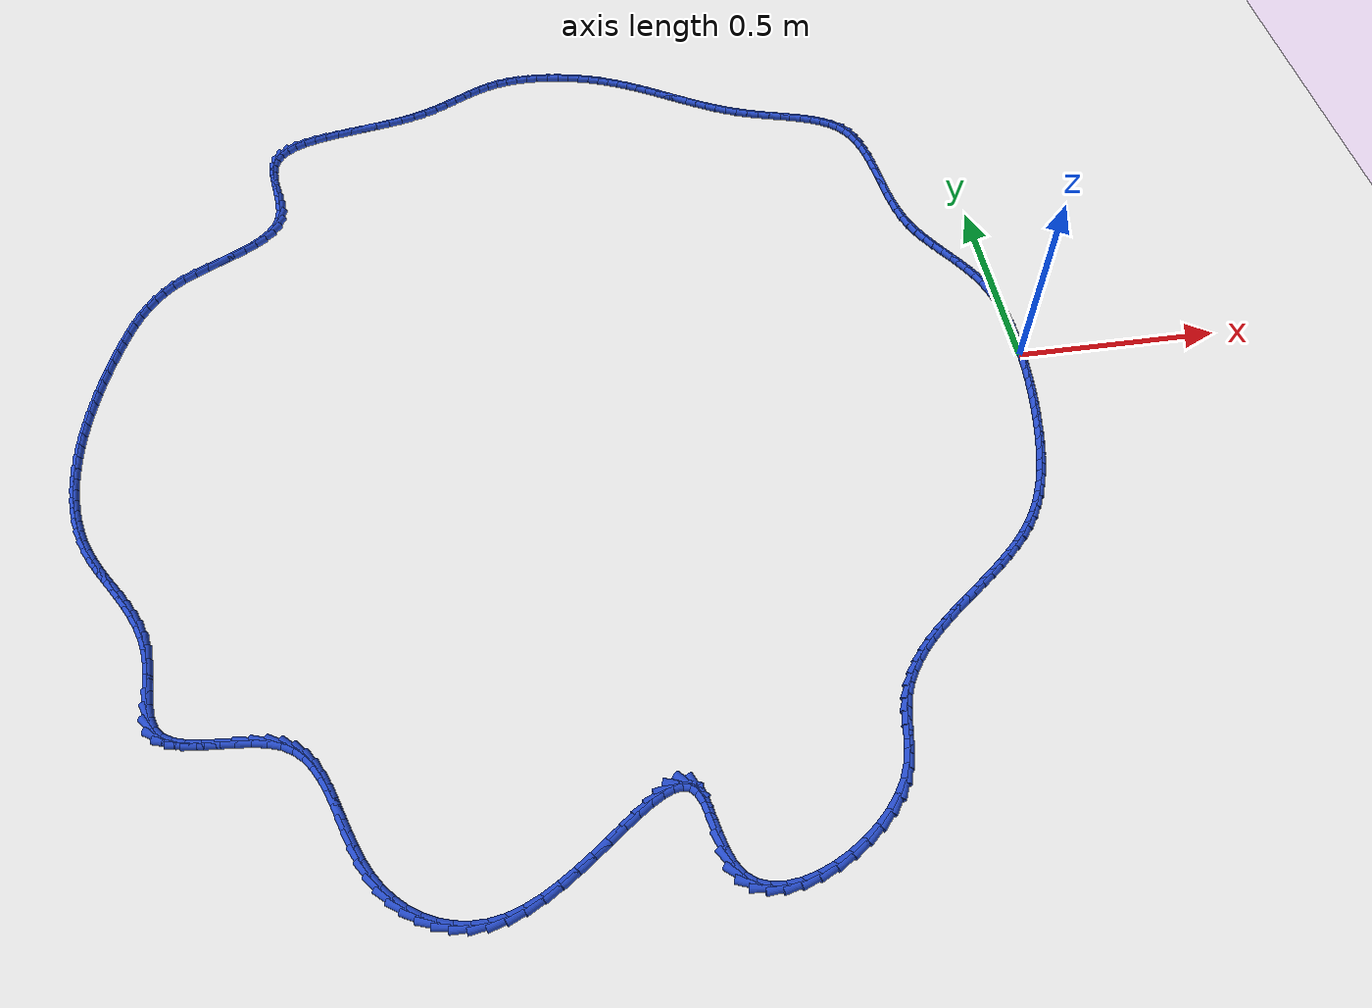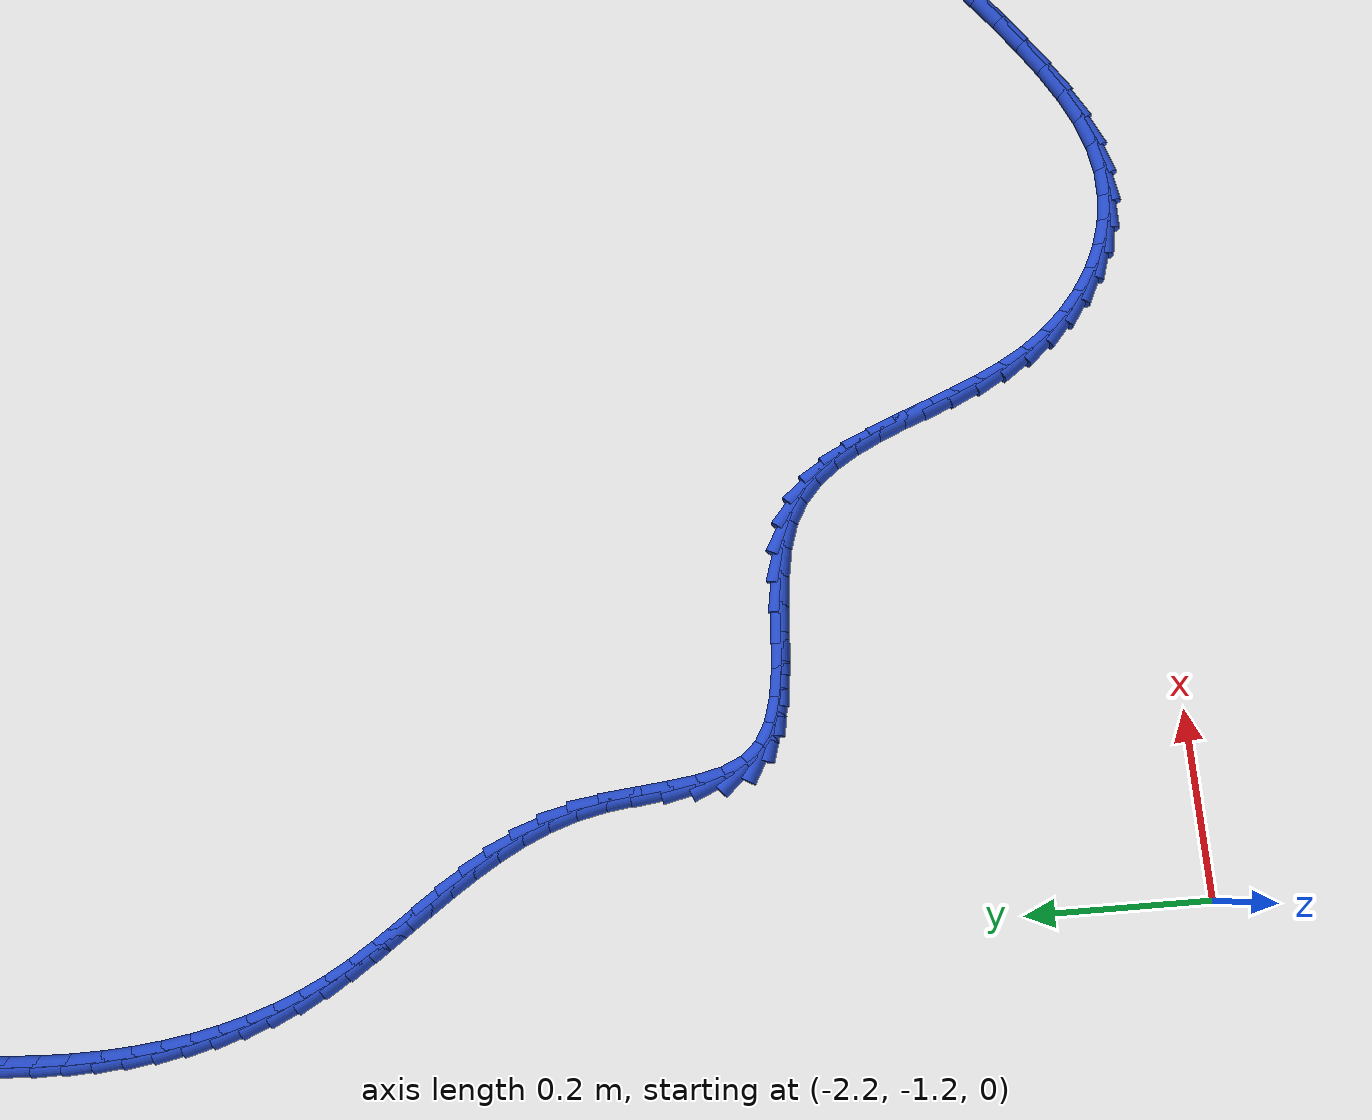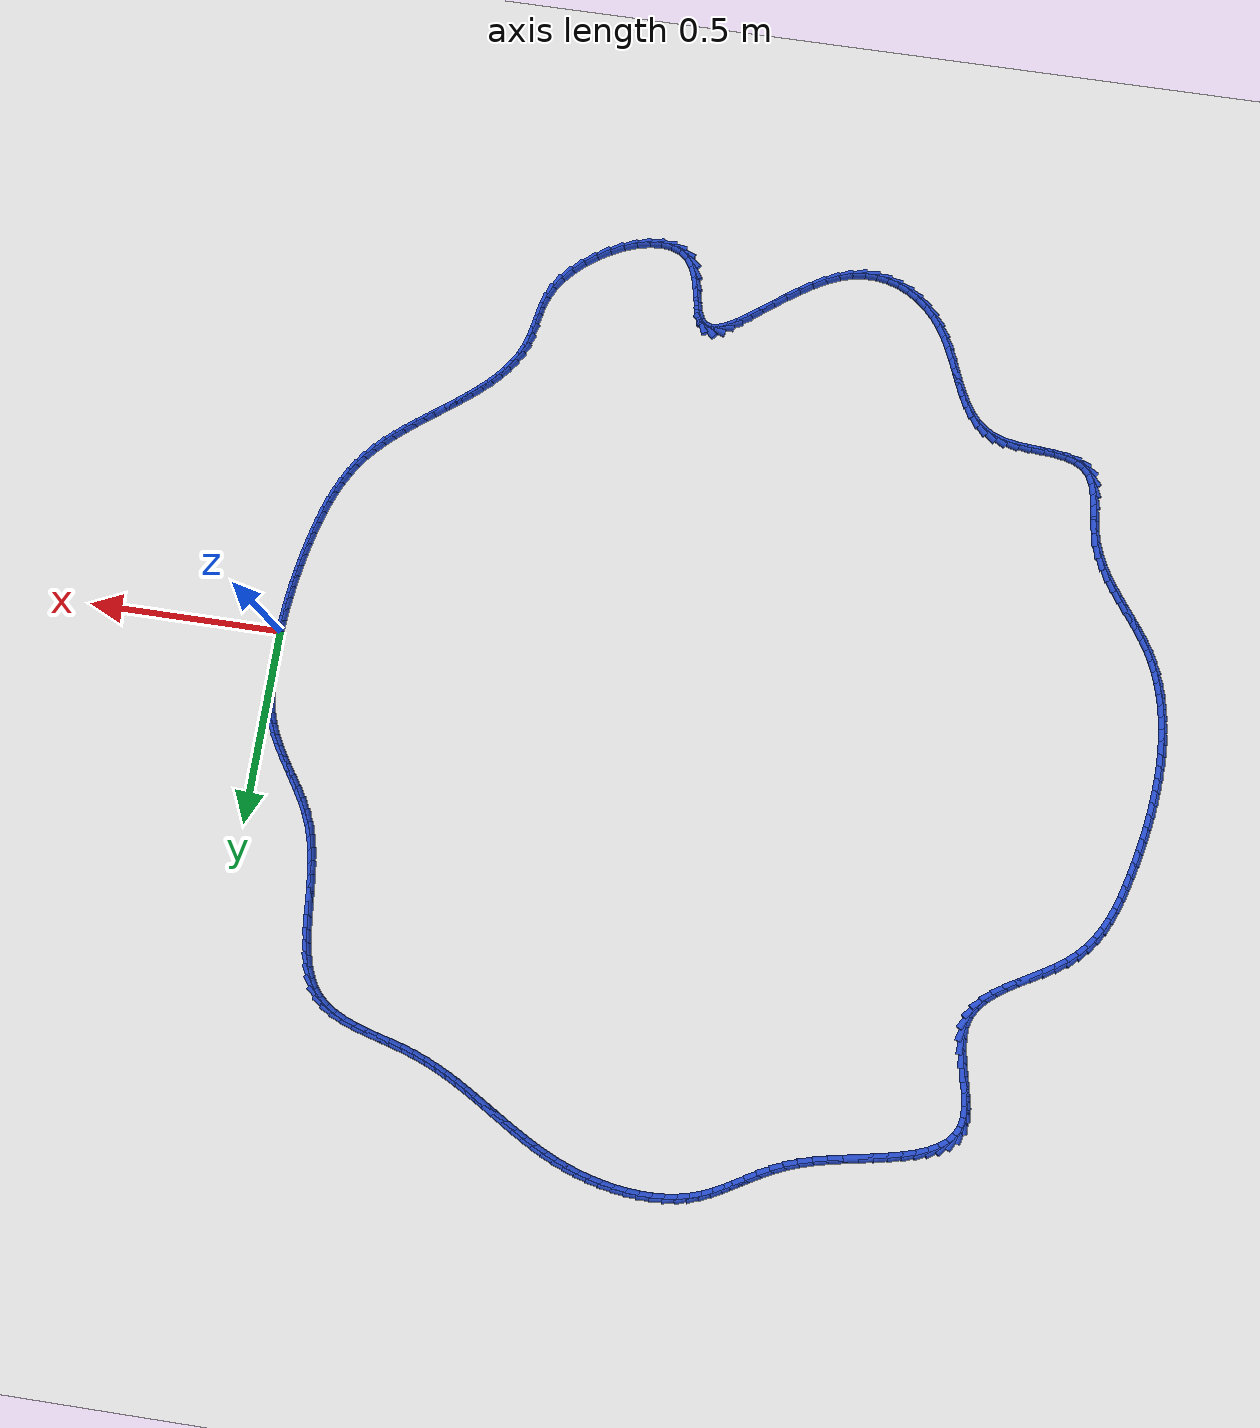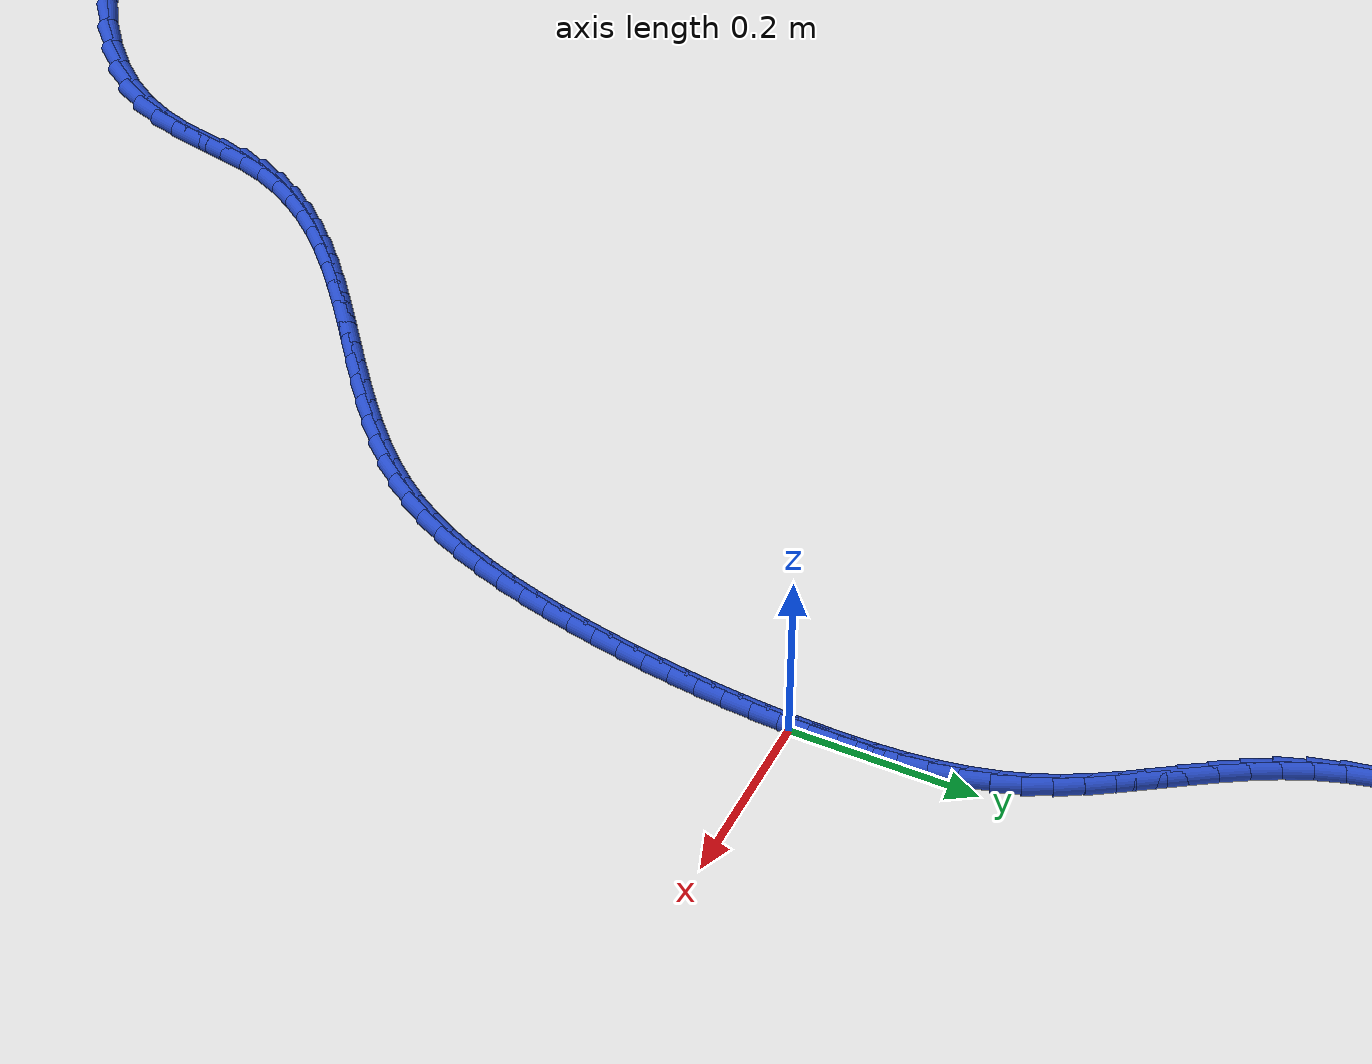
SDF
<sdf version="1.6">
 <world name="default">
  <light name="sun" type="directional">
   <pose>0 0 10 0 -0 0</pose>
   <diffuse>0.8 0.8 0.8 1</diffuse>
   <specular>0.2 0.2 0.2 1</specular>
   <attenuation>
    <range>1000</range>
    <constant>0.9</constant>
    <linear>0.01</linear>
    <quadratic>0.001</quadratic>
   </attenuation>
   <direction>-0.5 0.1 -0.9</direction>
  </light>
  <model name="ground_plane">
   <static>1</static>
   <link name="link">
    <collision name="collision">
     <geometry><plane><normal>0 0 1</normal><size>100 100</size></plane></geometry>
     <surface><friction><ode><mu>100</mu><mu2>50</mu2></ode></friction></surface>
    </collision>
    <visual name="visual">
     <cast_shadows>0</cast_shadows>
     <geometry><plane><normal>0 0 1</normal><size>100 100</size></plane></geometry>
     <material>
      <script><uri>file://media/materials/scripts/gazebo.material</uri><name>Gazebo/WhiteGlow</name></script>
     </material>
    </visual>
   </link>
  </model>
  <gravity>0 0 -9.8</gravity>
  <magnetic_field>6e-06 2.3e-05 -4.2e-05</magnetic_field>
  <atmosphere type="adiabatic"/>
  <physics name="default_physics" default="0" type="ode">
   <max_step_size>0.001</max_step_size>
   <real_time_factor>1</real_time_factor>
   <real_time_update_rate>1000</real_time_update_rate>
  </physics>
  <scene><ambient>0.4 0.4 0.4 1</ambient><background>0.7 0.7 0.7 1</background><shadows>1</shadows></scene>
  <spherical_coordinates>
   <surface_model>EARTH_WGS84</surface_model>
   <latitude_deg>0</latitude_deg>
   <longitude_deg>0</longitude_deg>
   <elevation>0</elevation>
   <heading_deg>0</heading_deg>
  </spherical_coordinates>
  <model name="line">
   <link name="link_0">
    <pose>-1.3986208025063007e-17 6.938893903907228e-18 0.01 0 1.57 1.541147706651697</pose>
    <collision name="collision">
     <geometry><cylinder><radius>0.01</radius><length>0.08</length></cylinder></geometry>
    </collision>
    <visual name="visual">
     <material>
      <script><name>Gazebo/Blue</name><uri>file://media/materials/scripts/gazebo.material</uri></script>
     </material>
     <geometry><cylinder><radius>0.01</radius><length>0.08</length></cylinder></geometry>
    </visual>
   </link>
   <link name="link_1">
    <pose>0.0009209669351892451 0.031053622702425017 0.01 0 1.57 1.5679352440857037</pose>
    <collision name="collision">
     <geometry><cylinder><radius>0.01</radius><length>0.08</length></cylinder></geometry>
    </collision>
    <visual name="visual">
     <material>
      <script><name>Gazebo/Blue</name><uri>file://media/materials/scripts/gazebo.material</uri></script>
     </material>
     <geometry><cylinder><radius>0.01</radius><length>0.08</length></cylinder></geometry>
    </visual>
   </link>
   <link name="link_2">
    <pose>0.0010101660360313475 0.06223023188148483 0.01 0 1.57 -1.539586764811051</pose>
    <collision name="collision">
     <geometry><cylinder><radius>0.01</radius><length>0.08</length></cylinder></geometry>
    </collision>
    <visual name="visual">
     <material>
      <script><name>Gazebo/Blue</name><uri>file://media/materials/scripts/gazebo.material</uri></script>
     </material>
     <geometry><cylinder><radius>0.01</radius><length>0.08</length></cylinder></geometry>
    </visual>
   </link>
   <link name="link_3">
    <pose>3.843940078641244e-05 0.09335566440451884 0.01 0 1.57 -1.4977291121396294</pose>
    <collision name="collision">
     <geometry><cylinder><radius>0.01</radius><length>0.08</length></cylinder></geometry>
    </collision>
    <visual name="visual">
     <material>
      <script><name>Gazebo/Blue</name><uri>file://media/materials/scripts/gazebo.material</uri></script>
     </material>
     <geometry><cylinder><radius>0.01</radius><length>0.08</length></cylinder></geometry>
    </visual>
   </link>
   <link name="link_4">
    <pose>-0.0022233708722854415 0.12425575713886644 0.01 0 1.57 -1.4474590469639808</pose>
    <collision name="collision">
     <geometry><cylinder><radius>0.01</radius><length>0.08</length></cylinder></geometry>
    </collision>
    <visual name="visual">
     <material>
      <script><name>Gazebo/Blue</name><uri>file://media/materials/scripts/gazebo.material</uri></script>
     </material>
     <geometry><cylinder><radius>0.01</radius><length>0.08</length></cylinder></geometry>
    </visual>
   </link>
   <link name="link_5">
    <pose>-0.0060044226849240954 0.154756346951867 0.01 0 1.57 -1.3880916904587615</pose>
    <collision name="collision">
     <geometry><cylinder><radius>0.01</radius><length>0.08</length></cylinder></geometry>
    </collision>
    <visual name="visual">
     <material>
      <script><name>Gazebo/Blue</name><uri>file://media/materials/scripts/gazebo.material</uri></script>
     </material>
     <geometry><cylinder><radius>0.01</radius><length>0.08</length></cylinder></geometry>
    </visual>
   </link>
   <link name="link_6">
    <pose>-0.011533873938869432 0.18468327071085983 0.01 0 1.57 -1.3189837926779546</pose>
    <collision name="collision">
     <geometry><cylinder><radius>0.01</radius><length>0.08</length></cylinder></geometry>
    </collision>
    <visual name="visual">
     <material>
      <script><name>Gazebo/Blue</name><uri>file://media/materials/scripts/gazebo.material</uri></script>
     </material>
     <geometry><cylinder><radius>0.01</radius><length>0.08</length></cylinder></geometry>
    </visual>
   </link>
   <link name="link_7">
    <pose>-0.019040882535861336 0.21386236528318442 0.01 0 1.57 -1.2396893328802263</pose>
    <collision name="collision">
     <geometry><cylinder><radius>0.01</radius><length>0.08</length></cylinder></geometry>
    </collision>
    <visual name="visual">
     <material>
      <script><name>Gazebo/Blue</name><uri>file://media/materials/scripts/gazebo.material</uri></script>
     </material>
     <geometry><cylinder><radius>0.01</radius><length>0.08</length></cylinder></geometry>
    </visual>
   </link>
   <link name="link_8">
    <pose>-0.028754606377639682 0.24211946753618002 0.01 0 1.57 -1.1524537851948669</pose>
    <collision name="collision">
     <geometry><cylinder><radius>0.01</radius><length>0.08</length></cylinder></geometry>
    </collision>
    <visual name="visual">
     <material>
      <script><name>Gazebo/Blue</name><uri>file://media/materials/scripts/gazebo.material</uri></script>
     </material>
     <geometry><cylinder><radius>0.01</radius><length>0.08</length></cylinder></geometry>
    </visual>
   </link>
   <link name="link_9">
    <pose>-0.04084561939749068 0.2693155839849843 0.01 0 1.57 -1.0770742326302656</pose>
    <collision name="collision">
     <geometry><cylinder><radius>0.01</radius><length>0.08</length></cylinder></geometry>
    </collision>
    <visual name="visual">
     <material>
      <script><name>Gazebo/Blue</name><uri>file://media/materials/scripts/gazebo.material</uri></script>
     </material>
     <geometry><cylinder><radius>0.01</radius><length>0.08</length></cylinder></geometry>
    </visual>
   </link>
   <link name="link_10">
    <pose>-0.054994497774060146 0.29560588094488843 0.01 0 1.57 -1.0237760894129433</pose>
    <collision name="collision">
     <geometry><cylinder><radius>0.01</radius><length>0.08</length></cylinder></geometry>
    </collision>
    <visual name="visual">
     <material>
      <script><name>Gazebo/Blue</name><uri>file://media/materials/scripts/gazebo.material</uri></script>
     </material>
     <geometry><cylinder><radius>0.01</radius><length>0.08</length></cylinder></geometry>
    </visual>
   </link>
   <link name="link_11">
    <pose>-0.07063771452956852 0.32129206690414536 0.01 0 1.57 -0.9924273753710027</pose>
    <collision name="collision">
     <geometry><cylinder><radius>0.01</radius><length>0.08</length></cylinder></geometry>
    </collision>
    <visual name="visual">
     <material>
      <script><name>Gazebo/Blue</name><uri>file://media/materials/scripts/gazebo.material</uri></script>
     </material>
     <geometry><cylinder><radius>0.01</radius><length>0.08</length></cylinder></geometry>
    </visual>
   </link>
   <link name="link_12">
    <pose>-0.08720995744448957 0.3466769220831745 0.01 0 1.57 -0.9824732555606587</pose>
    <collision name="collision">
     <geometry><cylinder><radius>0.01</radius><length>0.08</length></cylinder></geometry>
    </collision>
    <visual name="visual">
     <material>
      <script><name>Gazebo/Blue</name><uri>file://media/materials/scripts/gazebo.material</uri></script>
     </material>
     <geometry><cylinder><radius>0.01</radius><length>0.08</length></cylinder></geometry>
    </visual>
   </link>
   <link name="link_13">
    <pose>-0.10414591429929701 0.37206322670239567 0.01 0 1.57 -0.9934500000199725</pose>
    <collision name="collision">
     <geometry><cylinder><radius>0.01</radius><length>0.08</length></cylinder></geometry>
    </collision>
    <visual name="visual">
     <material>
      <script><name>Gazebo/Blue</name><uri>file://media/materials/scripts/gazebo.material</uri></script>
     </material>
     <geometry><cylinder><radius>0.01</radius><length>0.08</length></cylinder></geometry>
    </visual>
   </link>
   <link name="link_14">
    <pose>-0.12088027287446454 0.3977537609822283 0.01 0 1.57 -1.0251112106891256</pose>
    <collision name="collision">
     <geometry><cylinder><radius>0.01</radius><length>0.08</length></cylinder></geometry>
    </collision>
    <visual name="visual">
     <material>
      <script><name>Gazebo/Blue</name><uri>file://media/materials/scripts/gazebo.material</uri></script>
     </material>
     <geometry><cylinder><radius>0.01</radius><length>0.08</length></cylinder></geometry>
    </visual>
   </link>
   <link name="link_15">
    <pose>-0.13684772095046593 0.4240513051430922 0.01 0 1.57 -1.0772789710385027</pose>
    <collision name="collision">
     <geometry><cylinder><radius>0.01</radius><length>0.08</length></cylinder></geometry>
    </collision>
    <visual name="visual">
     <material>
      <script><name>Gazebo/Blue</name><uri>file://media/materials/scripts/gazebo.material</uri></script>
     </material>
     <geometry><cylinder><radius>0.01</radius><length>0.08</length></cylinder></geometry>
    </visual>
   </link>
   <link name="link_16">
    <pose>-0.15148294630777498 0.4512586394054071 0.01 0 1.57 -1.149443536979852</pose>
    <collision name="collision">
     <geometry><cylinder><radius>0.01</radius><length>0.08</length></cylinder></geometry>
    </collision>
    <visual name="visual">
     <material>
      <script><name>Gazebo/Blue</name><uri>file://media/materials/scripts/gazebo.material</uri></script>
     </material>
     <geometry><cylinder><radius>0.01</radius><length>0.08</length></cylinder></geometry>
    </visual>
   </link>
   <link name="link_17">
    <pose>-0.1642206367268653 0.47967854398959253 0.01 0 1.57 -1.2376838080199517</pose>
    <collision name="collision">
     <geometry><cylinder><radius>0.01</radius><length>0.08</length></cylinder></geometry>
    </collision>
    <visual name="visual">
     <material>
      <script><name>Gazebo/Blue</name><uri>file://media/materials/scripts/gazebo.material</uri></script>
     </material>
     <geometry><cylinder><radius>0.01</radius><length>0.08</length></cylinder></geometry>
    </visual>
   </link>
   <link name="link_18">
    <pose>-0.17456352236248238 0.5095707344833691 0.01 0 1.57 -1.3178588512926597</pose>
    <collision name="collision">
     <geometry><cylinder><radius>0.01</radius><length>0.08</length></cylinder></geometry>
    </collision>
    <visual name="visual">
     <material>
      <script><name>Gazebo/Blue</name><uri>file://media/materials/scripts/gazebo.material</uri></script>
     </material>
     <geometry><cylinder><radius>0.01</radius><length>0.08</length></cylinder></geometry>
    </visual>
   </link>
   <link name="link_19">
    <pose>-0.1826358559558088 0.5408015592208085 0.01 0 1.57 -1.3789601367383768</pose>
    <collision name="collision">
     <geometry><cylinder><radius>0.01</radius><length>0.08</length></cylinder></geometry>
    </collision>
    <visual name="visual">
     <material>
      <script><name>Gazebo/Blue</name><uri>file://media/materials/scripts/gazebo.material</uri></script>
     </material>
     <geometry><cylinder><radius>0.01</radius><length>0.08</length></cylinder></geometry>
    </visual>
   </link>
   <link name="link_20">
    <pose>-0.18889476864185656 0.5730266847965946 0.01 0 1.57 -1.4226556502023946</pose>
    <collision name="collision">
     <geometry><cylinder><radius>0.01</radius><length>0.08</length></cylinder></geometry>
    </collision>
    <visual name="visual">
     <material>
      <script><name>Gazebo/Blue</name><uri>file://media/materials/scripts/gazebo.material</uri></script>
     </material>
     <geometry><cylinder><radius>0.01</radius><length>0.08</length></cylinder></geometry>
    </visual>
   </link>
   <link name="link_21">
    <pose>-0.19380055047208625 0.6058997784986832 0.01 0 1.57 -1.4504173991615645</pose>
    <collision name="collision">
     <geometry><cylinder><radius>0.01</radius><length>0.08</length></cylinder></geometry>
    </collision>
    <visual name="visual">
     <material>
      <script><name>Gazebo/Blue</name><uri>file://media/materials/scripts/gazebo.material</uri></script>
     </material>
     <geometry><cylinder><radius>0.01</radius><length>0.08</length></cylinder></geometry>
    </visual>
   </link>
   <link name="link_22">
    <pose>-0.19781349149795885 0.6390745076150307 0.01 0 1.57 -1.4631432965136522</pose>
    <collision name="collision">
     <geometry><cylinder><radius>0.01</radius><length>0.08</length></cylinder></geometry>
    </collision>
    <visual name="visual">
     <material>
      <script><name>Gazebo/Blue</name><uri>file://media/materials/scripts/gazebo.material</uri></script>
     </material>
     <geometry><cylinder><radius>0.01</radius><length>0.08</length></cylinder></geometry>
    </visual>
   </link>
   <link name="link_23">
    <pose>-0.20139388177093517 0.6722045394335943 0.01 0 1.57 -1.4610303962927953</pose>
    <collision name="collision">
     <geometry><cylinder><radius>0.01</radius><length>0.08</length></cylinder></geometry>
    </collision>
    <visual name="visual">
     <material>
      <script><name>Gazebo/Blue</name><uri>file://media/materials/scripts/gazebo.material</uri></script>
     </material>
     <geometry><cylinder><radius>0.01</radius><length>0.08</length></cylinder></geometry>
    </visual>
   </link>
   <link name="link_24">
    <pose>-0.20500201134247611 0.7049435412423295 0.01 0 1.57 -1.4434901492613272</pose>
    <collision name="collision">
     <geometry><cylinder><radius>0.01</radius><length>0.08</length></cylinder></geometry>
    </collision>
    <visual name="visual">
     <material>
      <script><name>Gazebo/Blue</name><uri>file://media/materials/scripts/gazebo.material</uri></script>
     </material>
     <geometry><cylinder><radius>0.01</radius><length>0.08</length></cylinder></geometry>
    </visual>
   </link>
   <link name="link_25">
    <pose>-0.2090981702640424 0.7369451803291933 0.01 0 1.57 -1.4090644106940362</pose>
    <collision name="collision">
     <geometry><cylinder><radius>0.01</radius><length>0.08</length></cylinder></geometry>
    </collision>
    <visual name="visual">
     <material>
      <script><name>Gazebo/Blue</name><uri>file://media/materials/scripts/gazebo.material</uri></script>
     </material>
     <geometry><cylinder><radius>0.01</radius><length>0.08</length></cylinder></geometry>
    </visual>
   </link>
   <link name="link_26">
    <pose>-0.21414264858709503 0.7678631239821418 0.01 0 1.57 -1.3553542808637529</pose>
    <collision name="collision">
     <geometry><cylinder><radius>0.01</radius><length>0.08</length></cylinder></geometry>
    </collision>
    <visual name="visual">
     <material>
      <script><name>Gazebo/Blue</name><uri>file://media/materials/scripts/gazebo.material</uri></script>
     </material>
     <geometry><cylinder><radius>0.01</radius><length>0.08</length></cylinder></geometry>
    </visual>
   </link>
   <link name="link_27">
    <pose>-0.22059573636309462 0.7973510394891314 0.01 0 1.57 -1.2790574599209898</pose>
    <collision name="collision">
     <geometry><cylinder><radius>0.01</radius><length>0.08</length></cylinder></geometry>
    </collision>
    <visual name="visual">
     <material>
      <script><name>Gazebo/Blue</name><uri>file://media/materials/scripts/gazebo.material</uri></script>
     </material>
     <geometry><cylinder><radius>0.01</radius><length>0.08</length></cylinder></geometry>
    </visual>
   </link>
   <link name="link_28">
    <pose>-0.22891772364350227 0.8250625941381189 0.01 0 1.57 -1.1763665041440985</pose>
    <collision name="collision">
     <geometry><cylinder><radius>0.01</radius><length>0.08</length></cylinder></geometry>
    </collision>
    <visual name="visual">
     <material>
      <script><name>Gazebo/Blue</name><uri>file://media/materials/scripts/gazebo.material</uri></script>
     </material>
     <geometry><cylinder><radius>0.01</radius><length>0.08</length></cylinder></geometry>
    </visual>
   </link>
   <link name="link_29">
    <pose>-0.23956890047977863 0.85065145521706 0.01 0 1.57 -1.0442048724905517</pose>
    <collision name="collision">
     <geometry><cylinder><radius>0.01</radius><length>0.08</length></cylinder></geometry>
    </collision>
    <visual name="visual">
     <material>
      <script><name>Gazebo/Blue</name><uri>file://media/materials/scripts/gazebo.material</uri></script>
     </material>
     <geometry><cylinder><radius>0.01</radius><length>0.08</length></cylinder></geometry>
    </visual>
   </link>
   <link name="link_30">
    <pose>-0.25300955692338456 0.8737712900139115 0.01 0 1.57 -0.8827796427617055</pose>
    <collision name="collision">
     <geometry><cylinder><radius>0.01</radius><length>0.08</length></cylinder></geometry>
    </collision>
    <visual name="visual">
     <material>
      <script><name>Gazebo/Blue</name><uri>file://media/materials/scripts/gazebo.material</uri></script>
     </material>
     <geometry><cylinder><radius>0.01</radius><length>0.08</length></cylinder></geometry>
    </visual>
   </link>
   <link name="link_31">
    <pose>-0.269699983025781 0.8940757658166298 0.01 0 1.57 -0.7034686367013089</pose>
    <collision name="collision">
     <geometry><cylinder><radius>0.01</radius><length>0.08</length></cylinder></geometry>
    </collision>
    <visual name="visual">
     <material>
      <script><name>Gazebo/Blue</name><uri>file://media/materials/scripts/gazebo.material</uri></script>
     </material>
     <geometry><cylinder><radius>0.01</radius><length>0.08</length></cylinder></geometry>
    </visual>
   </link>
   <link name="link_32">
    <pose>-0.29000554535036516 0.9112996593205785 0.01 0 1.57 -0.5485828809500631</pose>
    <collision name="collision">
     <geometry><cylinder><radius>0.01</radius><length>0.08</length></cylinder></geometry>
    </collision>
    <visual name="visual">
     <material>
      <script><name>Gazebo/Blue</name><uri>file://media/materials/scripts/gazebo.material</uri></script>
     </material>
     <geometry><cylinder><radius>0.01</radius><length>0.08</length></cylinder></geometry>
    </visual>
   </link>
   <link name="link_33">
    <pose>-0.3136335221023308 0.9257400649134462 0.01 0 1.57 -0.43294949704175384</pose>
    <collision name="collision">
     <geometry><cylinder><radius>0.01</radius><length>0.08</length></cylinder></geometry>
    </collision>
    <visual name="visual">
     <material>
      <script><name>Gazebo/Blue</name><uri>file://media/materials/scripts/gazebo.material</uri></script>
     </material>
     <geometry><cylinder><radius>0.01</radius><length>0.08</length></cylinder></geometry>
    </visual>
   </link>
   <link name="link_34">
    <pose>-0.34001242000396475 0.9379322792471011 0.01 0 1.57 -0.35172746434491803</pose>
    <collision name="collision">
     <geometry><cylinder><radius>0.01</radius><length>0.08</length></cylinder></geometry>
    </collision>
    <visual name="visual">
     <material>
      <script><name>Gazebo/Blue</name><uri>file://media/materials/scripts/gazebo.material</uri></script>
     </material>
     <geometry><cylinder><radius>0.01</radius><length>0.08</length></cylinder></geometry>
    </visual>
   </link>
   <link name="link_35">
    <pose>-0.3685697426761781 0.9484124560948661 0.01 0 1.57 -0.29920421609278836</pose>
    <collision name="collision">
     <geometry><cylinder><radius>0.01</radius><length>0.08</length></cylinder></geometry>
    </collision>
    <visual name="visual">
     <material>
      <script><name>Gazebo/Blue</name><uri>file://media/materials/scripts/gazebo.material</uri></script>
     </material>
     <geometry><cylinder><radius>0.01</radius><length>0.08</length></cylinder></geometry>
    </visual>
   </link>
   <link name="link_36">
    <pose>-0.39873299373988236 0.957716749230064 0.01 0 1.57 -0.27091167237341246</pose>
    <collision name="collision">
     <geometry><cylinder><radius>0.01</radius><length>0.08</length></cylinder></geometry>
    </collision>
    <visual name="visual">
     <material>
      <script><name>Gazebo/Blue</name><uri>file://media/materials/scripts/gazebo.material</uri></script>
     </material>
     <geometry><cylinder><radius>0.01</radius><length>0.08</length></cylinder></geometry>
    </visual>
   </link>
   <link name="link_37">
    <pose>-0.4299296768159884 0.9663813124260171 0.01 0 1.57 -0.2641071932923933</pose>
    <collision name="collision">
     <geometry><cylinder><radius>0.01</radius><length>0.08</length></cylinder></geometry>
    </collision>
    <visual name="visual">
     <material>
      <script><name>Gazebo/Blue</name><uri>file://media/materials/scripts/gazebo.material</uri></script>
     </material>
     <geometry><cylinder><radius>0.01</radius><length>0.08</length></cylinder></geometry>
    </visual>
   </link>
   <link name="link_38">
    <pose>-0.461587295525408 0.9749422994560483 0.01 0 1.57 -0.2777252956315099</pose>
    <collision name="collision">
     <geometry><cylinder><radius>0.01</radius><length>0.08</length></cylinder></geometry>
    </collision>
    <visual name="visual">
     <material>
      <script><name>Gazebo/Blue</name><uri>file://media/materials/scripts/gazebo.material</uri></script>
     </material>
     <geometry><cylinder><radius>0.01</radius><length>0.08</length></cylinder></geometry>
    </visual>
   </link>
   <link name="link_39">
    <pose>-0.49313335348905224 0.9839358640934801 0.01 0 1.57 -0.31216639597460644</pose>
    <collision name="collision">
     <geometry><cylinder><radius>0.01</radius><length>0.08</length></cylinder></geometry>
    </collision>
    <visual name="visual">
     <material>
      <script><name>Gazebo/Blue</name><uri>file://media/materials/scripts/gazebo.material</uri></script>
     </material>
     <geometry><cylinder><radius>0.01</radius><length>0.08</length></cylinder></geometry>
    </visual>
   </link>
   <link name="link_40">
    <pose>-0.5239972693988119 0.993896200890041 0.01 0 1.57 -0.36011412033585544</pose>
    <collision name="collision">
     <geometry><cylinder><radius>0.01</radius><length>0.08</length></cylinder></geometry>
    </collision>
    <visual name="visual">
     <material>
      <script><name>Gazebo/Blue</name><uri>file://media/materials/scripts/gazebo.material</uri></script>
     </material>
     <geometry><cylinder><radius>0.01</radius><length>0.08</length></cylinder></geometry>
    </visual>
   </link>
   <link name="link_41">
    <pose>-0.5538311761620451 1.0051296556623404 0.01 0 1.57 -0.40478937362412876</pose>
    <collision name="collision">
     <geometry><cylinder><radius>0.01</radius><length>0.08</length></cylinder></geometry>
    </collision>
    <visual name="visual">
     <material>
      <script><name>Gazebo/Blue</name><uri>file://media/materials/scripts/gazebo.material</uri></script>
     </material>
     <geometry><cylinder><radius>0.01</radius><length>0.08</length></cylinder></geometry>
    </visual>
   </link>
   <link name="link_42">
    <pose>-0.5827149878514207 1.0175049308676767 0.01 0 1.57 -0.44364257790395245</pose>
    <collision name="collision">
     <geometry><cylinder><radius>0.01</radius><length>0.08</length></cylinder></geometry>
    </collision>
    <visual name="visual">
     <material>
      <script><name>Gazebo/Blue</name><uri>file://media/materials/scripts/gazebo.material</uri></script>
     </material>
     <geometry><cylinder><radius>0.01</radius><length>0.08</length></cylinder></geometry>
    </visual>
   </link>
   <link name="link_43">
    <pose>-0.6107771095930478 1.0308411199827654 0.01 0 1.57 -0.4761888184410632</pose>
    <collision name="collision">
     <geometry><cylinder><radius>0.01</radius><length>0.08</length></cylinder></geometry>
    </collision>
    <visual name="visual">
     <material>
      <script><name>Gazebo/Blue</name><uri>file://media/materials/scripts/gazebo.material</uri></script>
     </material>
     <geometry><cylinder><radius>0.01</radius><length>0.08</length></cylinder></geometry>
    </visual>
   </link>
   <link name="link_44">
    <pose>-0.6381459465130345 1.0449573164843207 0.01 0 1.57 -0.5020729780191528</pose>
    <collision name="collision">
     <geometry><cylinder><radius>0.01</radius><length>0.08</length></cylinder></geometry>
    </collision>
    <visual name="visual">
     <material>
      <script><name>Gazebo/Blue</name><uri>file://media/materials/scripts/gazebo.material</uri></script>
     </material>
     <geometry><cylinder><radius>0.01</radius><length>0.08</length></cylinder></geometry>
    </visual>
   </link>
   <link name="link_45">
    <pose>-0.6649499037374897 1.0596726138490573 0.01 0 1.57 -0.5210412539069489</pose>
    <collision name="collision">
     <geometry><cylinder><radius>0.01</radius><length>0.08</length></cylinder></geometry>
    </collision>
    <visual name="visual">
     <material>
      <script><name>Gazebo/Blue</name><uri>file://media/materials/scripts/gazebo.material</uri></script>
     </material>
     <geometry><cylinder><radius>0.01</radius><length>0.08</length></cylinder></geometry>
    </visual>
   </link>
   <link name="link_46">
    <pose>-0.6913173863925227 1.0748061055536908 0.01 0 1.57 -0.5329124336635036</pose>
    <collision name="collision">
     <geometry><cylinder><radius>0.01</radius><length>0.08</length></cylinder></geometry>
    </collision>
    <visual name="visual">
     <material>
      <script><name>Gazebo/Blue</name><uri>file://media/materials/scripts/gazebo.material</uri></script>
     </material>
     <geometry><cylinder><radius>0.01</radius><length>0.08</length></cylinder></geometry>
    </visual>
   </link>
   <link name="link_47">
    <pose>-0.7173767996042418 1.090176885074935 0.01 0 1.57 -0.5375538321107184</pose>
    <collision name="collision">
     <geometry><cylinder><radius>0.01</radius><length>0.08</length></cylinder></geometry>
    </collision>
    <visual name="visual">
     <material>
      <script><name>Gazebo/Blue</name><uri>file://media/materials/scripts/gazebo.material</uri></script>
     </material>
     <geometry><cylinder><radius>0.01</radius><length>0.08</length></cylinder></geometry>
    </visual>
   </link>
   <link name="link_48">
    <pose>-0.7432565484987558 1.105604045889505 0.01 0 1.57 -0.5348652059807022</pose>
    <collision name="collision">
     <geometry><cylinder><radius>0.01</radius><length>0.08</length></cylinder></geometry>
    </collision>
    <visual name="visual">
     <material>
      <script><name>Gazebo/Blue</name><uri>file://media/materials/scripts/gazebo.material</uri></script>
     </material>
     <geometry><cylinder><radius>0.01</radius><length>0.08</length></cylinder></geometry>
    </visual>
   </link>
   <link name="link_49">
    <pose>-0.7690850382021732 1.1209066814741158 0.01 0 1.57 -0.5247727653026203</pose>
    <collision name="collision">
     <geometry><cylinder><radius>0.01</radius><length>0.08</length></cylinder></geometry>
    </collision>
    <visual name="visual">
     <material>
      <script><name>Gazebo/Blue</name><uri>file://media/materials/scripts/gazebo.material</uri></script>
     </material>
     <geometry><cylinder><radius>0.01</radius><length>0.08</length></cylinder></geometry>
    </visual>
   </link>
   <link name="link_50">
    <pose>-0.7949906738406032 1.1359038853054824 0.01 0 1.57 -0.5072345987312812</pose>
    <collision name="collision">
     <geometry><cylinder><radius>0.01</radius><length>0.08</length></cylinder></geometry>
    </collision>
    <visual name="visual">
     <material>
      <script><name>Gazebo/Blue</name><uri>file://media/materials/scripts/gazebo.material</uri></script>
     </material>
     <geometry><cylinder><radius>0.01</radius><length>0.08</length></cylinder></geometry>
    </visual>
   </link>
   <link name="link_51">
    <pose>-0.8211018605401543 1.1504147508603186 0.01 0 1.57 -0.48225816670807825</pose>
    <collision name="collision">
     <geometry><cylinder><radius>0.01</radius><length>0.08</length></cylinder></geometry>
    </collision>
    <visual name="visual">
     <material>
      <script><name>Gazebo/Blue</name><uri>file://media/materials/scripts/gazebo.material</uri></script>
     </material>
     <geometry><cylinder><radius>0.01</radius><length>0.08</length></cylinder></geometry>
    </visual>
   </link>
   <link name="link_52">
    <pose>-0.8475470034269355 1.1642583716153405 0.01 0 1.57 -0.4499295834617749</pose>
    <collision name="collision">
     <geometry><cylinder><radius>0.01</radius><length>0.08</length></cylinder></geometry>
    </collision>
    <visual name="visual">
     <material>
      <script><name>Gazebo/Blue</name><uri>file://media/materials/scripts/gazebo.material</uri></script>
     </material>
     <geometry><cylinder><radius>0.01</radius><length>0.08</length></cylinder></geometry>
    </visual>
   </link>
   <link name="link_53">
    <pose>-0.8744545076270547 1.1772538410472617 0.01 0 1.57 -0.41049919189423534</pose>
    <collision name="collision">
     <geometry><cylinder><radius>0.01</radius><length>0.08</length></cylinder></geometry>
    </collision>
    <visual name="visual">
     <material>
      <script><name>Gazebo/Blue</name><uri>file://media/materials/scripts/gazebo.material</uri></script>
     </material>
     <geometry><cylinder><radius>0.01</radius><length>0.08</length></cylinder></geometry>
    </visual>
   </link>
   <link name="link_54">
    <pose>-0.9019514815904139 1.189221206723689 0.01 0 1.57 -0.3663580108797198</pose>
    <collision name="collision">
     <geometry><cylinder><radius>0.01</radius><length>0.08</length></cylinder></geometry>
    </collision>
    <visual name="visual">
     <material>
      <script><name>Gazebo/Blue</name><uri>file://media/materials/scripts/gazebo.material</uri></script>
     </material>
     <geometry><cylinder><radius>0.01</radius><length>0.08</length></cylinder></geometry>
    </visual>
   </link>
   <link name="link_55">
    <pose>-0.930106396688106 1.2000236612182433 0.01 0 1.57 -0.3205173660841436</pose>
    <collision name="collision">
     <geometry><cylinder><radius>0.01</radius><length>0.08</length></cylinder></geometry>
    </collision>
    <visual name="visual">
     <material>
      <script><name>Gazebo/Blue</name><uri>file://media/materials/scripts/gazebo.material</uri></script>
     </material>
     <geometry><cylinder><radius>0.01</radius><length>0.08</length></cylinder></geometry>
    </visual>
   </link>
   <link name="link_56">
    <pose>-0.9589064176205065 1.2095842223357571 0.01 0 1.57 -0.2732205005396671</pose>
    <collision name="collision">
     <geometry><cylinder><radius>0.01</radius><length>0.08</length></cylinder></geometry>
    </collision>
    <visual name="visual">
     <material>
      <script><name>Gazebo/Blue</name><uri>file://media/materials/scripts/gazebo.material</uri></script>
     </material>
     <geometry><cylinder><radius>0.01</radius><length>0.08</length></cylinder></geometry>
    </visual>
   </link>
   <link name="link_57">
    <pose>-0.9883327261002346 1.2178303101474781 0.01 0 1.57 -0.22452671844911645</pose>
    <collision name="collision">
     <geometry><cylinder><radius>0.01</radius><length>0.08</length></cylinder></geometry>
    </collision>
    <visual name="visual">
     <material>
      <script><name>Gazebo/Blue</name><uri>file://media/materials/scripts/gazebo.material</uri></script>
     </material>
     <geometry><cylinder><radius>0.01</radius><length>0.08</length></cylinder></geometry>
    </visual>
   </link>
   <link name="link_58">
    <pose>-1.0183665038399086 1.2246893447246536 0.01 0 1.57 -0.17450199606545194</pose>
    <collision name="collision">
     <geometry><cylinder><radius>0.01</radius><length>0.08</length></cylinder></geometry>
    </collision>
    <visual name="visual">
     <material>
      <script><name>Gazebo/Blue</name><uri>file://media/materials/scripts/gazebo.material</uri></script>
     </material>
     <geometry><cylinder><radius>0.01</radius><length>0.08</length></cylinder></geometry>
    </visual>
   </link>
   <link name="link_59">
    <pose>-1.048984261307572 1.2300871050368216 0.01 0 1.57 -0.12236379137889589</pose>
    <collision name="collision">
     <geometry><cylinder><radius>0.01</radius><length>0.08</length></cylinder></geometry>
    </collision>
    <visual name="visual">
     <material>
      <script><name>Gazebo/Blue</name><uri>file://media/materials/scripts/gazebo.material</uri></script>
     </material>
     <geometry><cylinder><radius>0.01</radius><length>0.08</length></cylinder></geometry>
    </visual>
   </link>
   <link name="link_60">
    <pose>-1.0800397950883858 1.2339062582104587 0.01 0 1.57 -0.0664365618793317</pose>
    <collision name="collision">
     <geometry><cylinder><radius>0.01</radius><length>0.08</length></cylinder></geometry>
    </collision>
    <visual name="visual">
     <material>
      <script><name>Gazebo/Blue</name><uri>file://media/materials/scripts/gazebo.material</uri></script>
     </material>
     <geometry><cylinder><radius>0.01</radius><length>0.08</length></cylinder></geometry>
    </visual>
   </link>
   <link name="link_61">
    <pose>-1.1112550492592892 1.2359831489469961 0.01 0 1.57 -0.005425694043413353</pose>
    <collision name="collision">
     <geometry><cylinder><radius>0.01</radius><length>0.08</length></cylinder></geometry>
    </collision>
    <visual name="visual">
     <material>
      <script><name>Gazebo/Blue</name><uri>file://media/materials/scripts/gazebo.material</uri></script>
     </material>
     <geometry><cylinder><radius>0.01</radius><length>0.08</length></cylinder></geometry>
    </visual>
   </link>
   <link name="link_62">
    <pose>-1.1423454659710004 1.2361518376910545 0.01 0 1.57 0.062025596062213036</pose>
    <collision name="collision">
     <geometry><cylinder><radius>0.01</radius><length>0.08</length></cylinder></geometry>
    </collision>
    <visual name="visual">
     <material>
      <script><name>Gazebo/Blue</name><uri>file://media/materials/scripts/gazebo.material</uri></script>
     </material>
     <geometry><cylinder><radius>0.01</radius><length>0.08</length></cylinder></geometry>
    </visual>
   </link>
   <link name="link_63">
    <pose>-1.1730264873742393 1.2342463848872556 0.01 0 1.57 0.1373733376233657</pose>
    <collision name="collision">
     <geometry><cylinder><radius>0.01</radius><length>0.08</length></cylinder></geometry>
    </collision>
    <visual name="visual">
     <material>
      <script><name>Gazebo/Blue</name><uri>file://media/materials/scripts/gazebo.material</uri></script>
     </material>
     <geometry><cylinder><radius>0.01</radius><length>0.08</length></cylinder></geometry>
    </visual>
   </link>
   <link name="link_64">
    <pose>-1.2030135556197248 1.23010085098022 0.01 0 1.57 0.2221224159318546</pose>
    <collision name="collision">
     <geometry><cylinder><radius>0.01</radius><length>0.08</length></cylinder></geometry>
    </collision>
    <visual name="visual">
     <material>
      <script><name>Gazebo/Blue</name><uri>file://media/materials/scripts/gazebo.material</uri></script>
     </material>
     <geometry><cylinder><radius>0.01</radius><length>0.08</length></cylinder></geometry>
    </visual>
   </link>
   <link name="link_65">
    <pose>-1.2320221128581752 1.2235492964145684 0.01 0 1.57 0.3161550049958404</pose>
    <collision name="collision">
     <geometry><cylinder><radius>0.01</radius><length>0.08</length></cylinder></geometry>
    </collision>
    <visual name="visual">
     <material>
      <script><name>Gazebo/Blue</name><uri>file://media/materials/scripts/gazebo.material</uri></script>
     </material>
     <geometry><cylinder><radius>0.01</radius><length>0.08</length></cylinder></geometry>
    </visual>
   </link>
   <link name="link_66">
    <pose>-1.2598034100361941 1.2144612682788094 0.01 0 1.57 0.4012670931757674</pose>
    <collision name="collision">
     <geometry><cylinder><radius>0.01</radius><length>0.08</length></cylinder></geometry>
    </collision>
    <visual name="visual">
     <material>
      <script><name>Gazebo/Blue</name><uri>file://media/materials/scripts/gazebo.material</uri></script>
     </material>
     <geometry><cylinder><radius>0.01</radius><length>0.08</length></cylinder></geometry>
    </visual>
   </link>
   <link name="link_67">
    <pose>-1.286528362119507 1.203122202194736 0.01 0 1.57 0.46299806849678915</pose>
    <collision name="collision">
     <geometry><cylinder><radius>0.01</radius><length>0.08</length></cylinder></geometry>
    </collision>
    <visual name="visual">
     <material>
      <script><name>Gazebo/Blue</name><uri>file://media/materials/scripts/gazebo.material</uri></script>
     </material>
     <geometry><cylinder><radius>0.01</radius><length>0.08</length></cylinder></geometry>
    </visual>
   </link>
   <link name="link_68">
    <pose>-1.3126402519467884 1.1900874513134838 0.01 0 1.57 0.49987390040384344</pose>
    <collision name="collision">
     <geometry><cylinder><radius>0.01</radius><length>0.08</length></cylinder></geometry>
    </collision>
    <visual name="visual">
     <material>
      <script><name>Gazebo/Blue</name><uri>file://media/materials/scripts/gazebo.material</uri></script>
     </material>
     <geometry><cylinder><radius>0.01</radius><length>0.08</length></cylinder></geometry>
    </visual>
   </link>
   <link name="link_69">
    <pose>-1.3385869750202228 1.1759169399521057 0.01 0 1.57 0.5121658748547565</pose>
    <collision name="collision">
     <geometry><cylinder><radius>0.01</radius><length>0.08</length></cylinder></geometry>
    </collision>
    <visual name="visual">
     <material>
      <script><name>Gazebo/Blue</name><uri>file://media/materials/scripts/gazebo.material</uri></script>
     </material>
     <geometry><cylinder><radius>0.01</radius><length>0.08</length></cylinder></geometry>
    </visual>
   </link>
   <link name="link_70">
    <pose>-1.3648164268419931 1.161170592427654 0.01 0 1.57 0.5009679637860345</pose>
    <collision name="collision">
     <geometry><cylinder><radius>0.01</radius><length>0.08</length></cylinder></geometry>
    </collision>
    <visual name="visual">
     <material>
      <script><name>Gazebo/Blue</name><uri>file://media/materials/scripts/gazebo.material</uri></script>
     </material>
     <geometry><cylinder><radius>0.01</radius><length>0.08</length></cylinder></geometry>
    </visual>
   </link>
   <link name="link_71">
    <pose>-1.3917765029142832 1.146408333057182 0.01 0 1.57 0.4678733604370564</pose>
    <collision name="collision">
     <geometry><cylinder><radius>0.01</radius><length>0.08</length></cylinder></geometry>
    </collision>
    <visual name="visual">
     <material>
      <script><name>Gazebo/Blue</name><uri>file://media/materials/scripts/gazebo.material</uri></script>
     </material>
     <geometry><cylinder><radius>0.01</radius><length>0.08</length></cylinder></geometry>
    </visual>
   </link>
   <link name="link_72">
    <pose>-1.4199150987392763 1.1321900861577419 0.01 0 1.57 0.4150051180495077</pose>
    <collision name="collision">
     <geometry><cylinder><radius>0.01</radius><length>0.08</length></cylinder></geometry>
    </collision>
    <visual name="visual">
     <material>
      <script><name>Gazebo/Blue</name><uri>file://media/materials/scripts/gazebo.material</uri></script>
     </material>
     <geometry><cylinder><radius>0.01</radius><length>0.08</length></cylinder></geometry>
    </visual>
   </link>
   <link name="link_73">
    <pose>-1.4496801098191556 1.1190757760463867 0.01 0 1.57 0.3459419176136435</pose>
    <collision name="collision">
     <geometry><cylinder><radius>0.01</radius><length>0.08</length></cylinder></geometry>
    </collision>
    <visual name="visual">
     <material>
      <script><name>Gazebo/Blue</name><uri>file://media/materials/scripts/gazebo.material</uri></script>
     </material>
     <geometry><cylinder><radius>0.01</radius><length>0.08</length></cylinder></geometry>
    </visual>
   </link>
   <link name="link_74">
    <pose>-1.48149953530145 1.1076068947423887 0.01 0 1.57 0.28044574800079436</pose>
    <collision name="collision">
     <geometry><cylinder><radius>0.01</radius><length>0.08</length></cylinder></geometry>
    </collision>
    <visual name="visual">
     <material>
      <script><name>Gazebo/Blue</name><uri>file://media/materials/scripts/gazebo.material</uri></script>
     </material>
     <geometry><cylinder><radius>0.01</radius><length>0.08</length></cylinder></geometry>
    </visual>
   </link>
   <link name="link_75">
    <pose>-1.515308775446236 1.097868582861101 0.01 0 1.57 0.23405546858715767</pose>
    <collision name="collision">
     <geometry><cylinder><radius>0.01</radius><length>0.08</length></cylinder></geometry>
    </collision>
    <visual name="visual">
     <material>
      <script><name>Gazebo/Blue</name><uri>file://media/materials/scripts/gazebo.material</uri></script>
     </material>
     <geometry><cylinder><radius>0.01</radius><length>0.08</length></cylinder></geometry>
    </visual>
   </link>
   <link name="link_76">
    <pose>-1.550530375425055 1.0894708639487523 0.01 0 1.57 0.2043979444478641</pose>
    <collision name="collision">
     <geometry><cylinder><radius>0.01</radius><length>0.08</length></cylinder></geometry>
    </collision>
    <visual name="visual">
     <material>
      <script><name>Gazebo/Blue</name><uri>file://media/materials/scripts/gazebo.material</uri></script>
     </material>
     <geometry><cylinder><radius>0.01</radius><length>0.08</length></cylinder></geometry>
    </visual>
   </link>
   <link name="link_77">
    <pose>-1.5865629307520834 1.0820015742100233 0.01 0 1.57 0.18954624996845568</pose>
    <collision name="collision">
     <geometry><cylinder><radius>0.01</radius><length>0.08</length></cylinder></geometry>
    </collision>
    <visual name="visual">
     <material>
      <script><name>Gazebo/Blue</name><uri>file://media/materials/scripts/gazebo.material</uri></script>
     </material>
     <geometry><cylinder><radius>0.01</radius><length>0.08</length></cylinder></geometry>
    </visual>
   </link>
   <link name="link_78">
    <pose>-1.6228050369414995 1.075048549849596 0.01 0 1.57 0.18876795513011335</pose>
    <collision name="collision">
     <geometry><cylinder><radius>0.01</radius><length>0.08</length></cylinder></geometry>
    </collision>
    <visual name="visual">
     <material>
      <script><name>Gazebo/Blue</name><uri>file://media/materials/scripts/gazebo.material</uri></script>
     </material>
     <geometry><cylinder><radius>0.01</radius><length>0.08</length></cylinder></geometry>
    </visual>
   </link>
   <link name="link_79">
    <pose>-1.6586552895074813 1.068199627072153 0.01 0 1.57 0.20250971545210233</pose>
    <collision name="collision">
     <geometry><cylinder><radius>0.01</radius><length>0.08</length></cylinder></geometry>
    </collision>
    <visual name="visual">
     <material>
      <script><name>Gazebo/Blue</name><uri>file://media/materials/scripts/gazebo.material</uri></script>
     </material>
     <geometry><cylinder><radius>0.01</radius><length>0.08</length></cylinder></geometry>
    </visual>
   </link>
   <link name="link_80">
    <pose>-1.6935122839642058 1.0610426420823758 0.01 0 1.57 0.23253673835171096</pose>
    <collision name="collision">
     <geometry><cylinder><radius>0.01</radius><length>0.08</length></cylinder></geometry>
    </collision>
    <visual name="visual">
     <material>
      <script><name>Gazebo/Blue</name><uri>file://media/materials/scripts/gazebo.material</uri></script>
     </material>
     <geometry><cylinder><radius>0.01</radius><length>0.08</length></cylinder></geometry>
    </visual>
   </link>
   <link name="link_81">
    <pose>-1.7267746158258503 1.0531654310849454 0.01 0 1.57 0.2822688241438516</pose>
    <collision name="collision">
     <geometry><cylinder><radius>0.01</radius><length>0.08</length></cylinder></geometry>
    </collision>
    <visual name="visual">
     <material>
      <script><name>Gazebo/Blue</name><uri>file://media/materials/scripts/gazebo.material</uri></script>
     </material>
     <geometry><cylinder><radius>0.01</radius><length>0.08</length></cylinder></geometry>
    </visual>
   </link>
   <link name="link_82">
    <pose>-1.7578408806065937 1.0441558302845448 0.01 0 1.57 0.35732332483588025</pose>
    <collision name="collision">
     <geometry><cylinder><radius>0.01</radius><length>0.08</length></cylinder></geometry>
    </collision>
    <visual name="visual">
     <material>
      <script><name>Gazebo/Blue</name><uri>file://media/materials/scripts/gazebo.material</uri></script>
     </material>
     <geometry><cylinder><radius>0.01</radius><length>0.08</length></cylinder></geometry>
    </visual>
   </link>
   <link name="link_83">
    <pose>-1.7861096738206117 1.0336016758858548 0.01 0 1.57 0.4660865551839481</pose>
    <collision name="collision">
     <geometry><cylinder><radius>0.01</radius><length>0.08</length></cylinder></geometry>
    </collision>
    <visual name="visual">
     <material>
      <script><name>Gazebo/Blue</name><uri>file://media/materials/scripts/gazebo.material</uri></script>
     </material>
     <geometry><cylinder><radius>0.01</radius><length>0.08</length></cylinder></geometry>
    </visual>
   </link>
   <link name="link_84">
    <pose>-1.8109795909820836 1.0210908040935578 0.01 0 1.57 0.6193881523407391</pose>
    <collision name="collision">
     <geometry><cylinder><radius>0.01</radius><length>0.08</length></cylinder></geometry>
    </collision>
    <visual name="visual">
     <material>
      <script><name>Gazebo/Blue</name><uri>file://media/materials/scripts/gazebo.material</uri></script>
     </material>
     <geometry><cylinder><radius>0.01</radius><length>0.08</length></cylinder></geometry>
    </visual>
   </link>
   <link name="link_85">
    <pose>-1.8318492276051863 1.0062110511123357 0.01 0 1.57 0.8264272237578307</pose>
    <collision name="collision">
     <geometry><cylinder><radius>0.01</radius><length>0.08</length></cylinder></geometry>
    </collision>
    <visual name="visual">
     <material>
      <script><name>Gazebo/Blue</name><uri>file://media/materials/scripts/gazebo.material</uri></script>
     </material>
     <geometry><cylinder><radius>0.01</radius><length>0.08</length></cylinder></geometry>
    </visual>
   </link>
   <link name="link_86">
    <pose>-1.8481171792040971 0.9885502531468697 0.01 0 1.57 1.0829796913932284</pose>
    <collision name="collision">
     <geometry><cylinder><radius>0.01</radius><length>0.08</length></cylinder></geometry>
    </collision>
    <visual name="visual">
     <material>
      <script><name>Gazebo/Blue</name><uri>file://media/materials/scripts/gazebo.material</uri></script>
     </material>
     <geometry><cylinder><radius>0.01</radius><length>0.08</length></cylinder></geometry>
    </visual>
   </link>
   <link name="link_87">
    <pose>-1.859182041292994 0.9676962464018419 0.01 0 1.57 1.3576406347853465</pose>
    <collision name="collision">
     <geometry><cylinder><radius>0.01</radius><length>0.08</length></cylinder></geometry>
    </collision>
    <visual name="visual">
     <material>
      <script><name>Gazebo/Blue</name><uri>file://media/materials/scripts/gazebo.material</uri></script>
     </material>
     <geometry><cylinder><radius>0.01</radius><length>0.08</length></cylinder></geometry>
    </visual>
   </link>
   <link name="link_88">
    <pose>-1.8644722845696735 0.9432545900085475 0.01 0 1.57 -1.5681867805016165</pose>
    <collision name="collision">
     <geometry><cylinder><radius>0.01</radius><length>0.08</length></cylinder></geometry>
    </collision>
    <visual name="visual">
     <material>
      <script><name>Gazebo/Blue</name><uri>file://media/materials/scripts/gazebo.material</uri></script>
     </material>
     <geometry><cylinder><radius>0.01</radius><length>0.08</length></cylinder></geometry>
    </visual>
   </link>
   <link name="link_89">
    <pose>-1.8643996334644077 0.915414141061054 0.01 0 1.57 -1.444903750423835</pose>
    <collision name="collision">
     <geometry><cylinder><radius>0.01</radius><length>0.08</length></cylinder></geometry>
    </collision>
    <visual name="visual">
     <material>
      <script><name>Gazebo/Blue</name><uri>file://media/materials/scripts/gazebo.material</uri></script>
     </material>
     <geometry><cylinder><radius>0.01</radius><length>0.08</length></cylinder></geometry>
    </visual>
   </link>
   <link name="link_90">
    <pose>-1.8605586454097436 0.8850654515036408 0.01 0 1.57 -1.3866995117534495</pose>
    <collision name="collision">
     <geometry><cylinder><radius>0.01</radius><length>0.08</length></cylinder></geometry>
    </collision>
    <visual name="visual">
     <material>
      <script><name>Gazebo/Blue</name><uri>file://media/materials/scripts/gazebo.material</uri></script>
     </material>
     <geometry><cylinder><radius>0.01</radius><length>0.08</length></cylinder></geometry>
    </visual>
   </link>
   <link name="link_91">
    <pose>-1.8546140966867697 0.8531407293760073 0.01 0 1.57 -1.3772528796642394</pose>
    <collision name="collision">
     <geometry><cylinder><radius>0.01</radius><length>0.08</length></cylinder></geometry>
    </collision>
    <visual name="visual">
     <material>
      <script><name>Gazebo/Blue</name><uri>file://media/materials/scripts/gazebo.material</uri></script>
     </material>
     <geometry><cylinder><radius>0.01</radius><length>0.08</length></cylinder></geometry>
    </visual>
   </link>
   <link name="link_92">
    <pose>-1.8482307635765753 0.8205721827178533 0.01 0 1.57 -1.4123671576766212</pose>
    <collision name="collision">
     <geometry><cylinder><radius>0.01</radius><length>0.08</length></cylinder></geometry>
    </collision>
    <visual name="visual">
     <material>
      <script><name>Gazebo/Blue</name><uri>file://media/materials/scripts/gazebo.material</uri></script>
     </material>
     <geometry><cylinder><radius>0.01</radius><length>0.08</length></cylinder></geometry>
    </visual>
   </link>
   <link name="link_93">
    <pose>-1.8430734223602487 0.7882920195688786 0.01 0 1.57 -1.4979504278680298</pose>
    <collision name="collision">
     <geometry><cylinder><radius>0.01</radius><length>0.08</length></cylinder></geometry>
    </collision>
    <visual name="visual">
     <material>
      <script><name>Gazebo/Blue</name><uri>file://media/materials/scripts/gazebo.material</uri></script>
     </material>
     <geometry><cylinder><radius>0.01</radius><length>0.08</length></cylinder></geometry>
    </visual>
   </link>
   <link name="link_94">
    <pose>-1.8408068493188792 0.757232447968783 0.01 0 1.57 1.4917765999496022</pose>
    <collision name="collision">
     <geometry><cylinder><radius>0.01</radius><length>0.08</length></cylinder></geometry>
    </collision>
    <visual name="visual">
     <material>
      <script><name>Gazebo/Blue</name><uri>file://media/materials/scripts/gazebo.material</uri></script>
     </material>
     <geometry><cylinder><radius>0.01</radius><length>0.08</length></cylinder></geometry>
    </visual>
   </link>
   <link name="link_95">
    <pose>-1.8430958207335546 0.7283256759572656 0.01 0 1.57 1.262140762932919</pose>
    <collision name="collision">
     <geometry><cylinder><radius>0.01</radius><length>0.08</length></cylinder></geometry>
    </collision>
    <visual name="visual">
     <material>
      <script><name>Gazebo/Blue</name><uri>file://media/materials/scripts/gazebo.material</uri></script>
     </material>
     <geometry><cylinder><radius>0.01</radius><length>0.08</length></cylinder></geometry>
    </visual>
   </link>
   <link name="link_96">
    <pose>-1.8513705018904636 0.7023736880328515 0.01 0 1.57 1.0245258376319855</pose>
    <collision name="collision">
     <geometry><cylinder><radius>0.01</radius><length>0.08</length></cylinder></geometry>
    </collision>
    <visual name="visual">
     <material>
      <script><name>Gazebo/Blue</name><uri>file://media/materials/scripts/gazebo.material</uri></script>
     </material>
     <geometry><cylinder><radius>0.01</radius><length>0.08</length></cylinder></geometry>
    </visual>
   </link>
   <link name="link_97">
    <pose>-1.8654190127287424 0.6792670324676728 0.01 0 1.57 0.8320299157422221</pose>
    <collision name="collision">
     <geometry><cylinder><radius>0.01</radius><length>0.08</length></cylinder></geometry>
    </collision>
    <visual name="visual">
     <material>
      <script><name>Gazebo/Blue</name><uri>file://media/materials/scripts/gazebo.material</uri></script>
     </material>
     <geometry><cylinder><radius>0.01</radius><length>0.08</length></cylinder></geometry>
    </visual>
   </link>
   <link name="link_98">
    <pose>-1.8843279782514444 0.6585068846712141 0.01 0 1.57 0.6913566276712136</pose>
    <collision name="collision">
     <geometry><cylinder><radius>0.01</radius><length>0.08</length></cylinder></geometry>
    </collision>
    <visual name="visual">
     <material>
      <script><name>Gazebo/Blue</name><uri>file://media/materials/scripts/gazebo.material</uri></script>
     </material>
     <geometry><cylinder><radius>0.01</radius><length>0.08</length></cylinder></geometry>
    </visual>
   </link>
   <link name="link_99">
    <pose>-1.9071813896208427 0.6395929581092292 0.01 0 1.57 0.5963395808274556</pose>
    <collision name="collision">
     <geometry><cylinder><radius>0.01</radius><length>0.08</length></cylinder></geometry>
    </collision>
    <visual name="visual">
     <material>
      <script><name>Gazebo/Blue</name><uri>file://media/materials/scripts/gazebo.material</uri></script>
     </material>
     <geometry><cylinder><radius>0.01</radius><length>0.08</length></cylinder></geometry>
    </visual>
   </link>
   <link name="link_100">
    <pose>-1.9330632379992099 0.6220249662474714 0.01 0 1.57 0.5384677079357206</pose>
    <collision name="collision">
     <geometry><cylinder><radius>0.01</radius><length>0.08</length></cylinder></geometry>
    </collision>
    <visual name="visual">
     <material>
      <script><name>Gazebo/Blue</name><uri>file://media/materials/scripts/gazebo.material</uri></script>
     </material>
     <geometry><cylinder><radius>0.01</radius><length>0.08</length></cylinder></geometry>
    </visual>
   </link>
   <link name="link_101">
    <pose>-1.9610575145488176 0.6053026225516939 0.01 0 1.57 0.5112753642001465</pose>
    <collision name="collision">
     <geometry><cylinder><radius>0.01</radius><length>0.08</length></cylinder></geometry>
    </collision>
    <visual name="visual">
     <material>
      <script><name>Gazebo/Blue</name><uri>file://media/materials/scripts/gazebo.material</uri></script>
     </material>
     <geometry><cylinder><radius>0.01</radius><length>0.08</length></cylinder></geometry>
    </visual>
   </link>
   <link name="link_102">
    <pose>-1.9902482104319392 0.58892564048765 0.01 0 1.57 0.5112135512822906</pose>
    <collision name="collision">
     <geometry><cylinder><radius>0.01</radius><length>0.08</length></cylinder></geometry>
    </collision>
    <visual name="visual">
     <material>
      <script><name>Gazebo/Blue</name><uri>file://media/materials/scripts/gazebo.material</uri></script>
     </material>
     <geometry><cylinder><radius>0.01</radius><length>0.08</length></cylinder></geometry>
    </visual>
   </link>
   <link name="link_103">
    <pose>-2.0197193168108467 0.5723937335210932 0.01 0 1.57 0.537502704024936</pose>
    <collision name="collision">
     <geometry><cylinder><radius>0.01</radius><length>0.08</length></cylinder></geometry>
    </collision>
    <visual name="visual">
     <material>
      <script><name>Gazebo/Blue</name><uri>file://media/materials/scripts/gazebo.material</uri></script>
     </material>
     <geometry><cylinder><radius>0.01</radius><length>0.08</length></cylinder></geometry>
    </visual>
   </link>
   <link name="link_104">
    <pose>-2.0485548248478143 0.5552066151177771 0.01 0 1.57 0.5918836309870299</pose>
    <collision name="collision">
     <geometry><cylinder><radius>0.01</radius><length>0.08</length></cylinder></geometry>
    </collision>
    <visual name="visual">
     <material>
      <script><name>Gazebo/Blue</name><uri>file://media/materials/scripts/gazebo.material</uri></script>
     </material>
     <geometry><cylinder><radius>0.01</radius><length>0.08</length></cylinder></geometry>
    </visual>
   </link>
   <link name="link_105">
    <pose>-2.075838725705111 0.5368639987434548 0.01 0 1.57 0.6782758042307528</pose>
    <collision name="collision">
     <geometry><cylinder><radius>0.01</radius><length>0.08</length></cylinder></geometry>
    </collision>
    <visual name="visual">
     <material>
      <script><name>Gazebo/Blue</name><uri>file://media/materials/scripts/gazebo.material</uri></script>
     </material>
     <geometry><cylinder><radius>0.01</radius><length>0.08</length></cylinder></geometry>
    </visual>
   </link>
   <link name="link_106">
    <pose>-2.1006558146092376 0.5168660500432628 0.01 0 1.57 0.7903277123077719</pose>
    <collision name="collision">
     <geometry><cylinder><radius>0.01</radius><length>0.08</length></cylinder></geometry>
    </collision>
    <visual name="visual">
     <material>
      <script><name>Gazebo/Blue</name><uri>file://media/materials/scripts/gazebo.material</uri></script>
     </material>
     <geometry><cylinder><radius>0.01</radius><length>0.08</length></cylinder></geometry>
    </visual>
   </link>
   <link name="link_107">
    <pose>-2.1224124997302964 0.49489379924768917 0.01 0 1.57 0.8994665018333661</pose>
    <collision name="collision">
     <geometry><cylinder><radius>0.01</radius><length>0.08</length></cylinder></geometry>
    </collision>
    <visual name="visual">
     <material>
      <script><name>Gazebo/Blue</name><uri>file://media/materials/scripts/gazebo.material</uri></script>
     </material>
     <geometry><cylinder><radius>0.01</radius><length>0.08</length></cylinder></geometry>
    </visual>
   </link>
   <link name="link_108">
    <pose>-2.141326901984766 0.47108475724888277 0.01 0 1.57 0.9976891044029345</pose>
    <collision name="collision">
     <geometry><cylinder><radius>0.01</radius><length>0.08</length></cylinder></geometry>
    </collision>
    <visual name="visual">
     <material>
      <script><name>Gazebo/Blue</name><uri>file://media/materials/scripts/gazebo.material</uri></script>
     </material>
     <geometry><cylinder><radius>0.01</radius><length>0.08</length></cylinder></geometry>
    </visual>
   </link>
   <link name="link_109">
    <pose>-2.1577432227931705 0.44564733848481786 0.01 0 1.57 1.0826233466722737</pose>
    <collision name="collision">
     <geometry><cylinder><radius>0.01</radius><length>0.08</length></cylinder></geometry>
    </collision>
    <visual name="visual">
     <material>
      <script><name>Gazebo/Blue</name><uri>file://media/materials/scripts/gazebo.material</uri></script>
     </material>
     <geometry><cylinder><radius>0.01</radius><length>0.08</length></cylinder></geometry>
    </visual>
   </link>
   <link name="link_110">
    <pose>-2.1720056635760328 0.418789957393469 0.01 0 1.57 1.1532361355497558</pose>
    <collision name="collision">
     <geometry><cylinder><radius>0.01</radius><length>0.08</length></cylinder></geometry>
    </collision>
    <visual name="visual">
     <material>
      <script><name>Gazebo/Blue</name><uri>file://media/materials/scripts/gazebo.material</uri></script>
     </material>
     <geometry><cylinder><radius>0.01</radius><length>0.08</length></cylinder></geometry>
    </visual>
   </link>
   <link name="link_111">
    <pose>-2.184458425753877 0.39072102841281053 0.01 0 1.57 1.2094569460566007</pose>
    <collision name="collision">
     <geometry><cylinder><radius>0.01</radius><length>0.08</length></cylinder></geometry>
    </collision>
    <visual name="visual">
     <material>
      <script><name>Gazebo/Blue</name><uri>file://media/materials/scripts/gazebo.material</uri></script>
     </material>
     <geometry><cylinder><radius>0.01</radius><length>0.08</length></cylinder></geometry>
    </visual>
   </link>
   <link name="link_112">
    <pose>-2.1954457107472285 0.36164896598081736 0.01 0 1.57 1.2517477222894497</pose>
    <collision name="collision">
     <geometry><cylinder><radius>0.01</radius><length>0.08</length></cylinder></geometry>
    </collision>
    <visual name="visual">
     <material>
      <script><name>Gazebo/Blue</name><uri>file://media/materials/scripts/gazebo.material</uri></script>
     </material>
     <geometry><cylinder><radius>0.01</radius><length>0.08</length></cylinder></geometry>
    </visual>
   </link>
   <link name="link_113">
    <pose>-2.20531171997661 0.3317821845354638 0.01 0 1.57 1.2807682912476095</pose>
    <collision name="collision">
     <geometry><cylinder><radius>0.01</radius><length>0.08</length></cylinder></geometry>
    </collision>
    <visual name="visual">
     <material>
      <script><name>Gazebo/Blue</name><uri>file://media/materials/scripts/gazebo.material</uri></script>
     </material>
     <geometry><cylinder><radius>0.01</radius><length>0.08</length></cylinder></geometry>
    </visual>
   </link>
   <link name="link_114">
    <pose>-2.2144002781715124 0.3013289707490363 0.01 0 1.57 1.3007832867178366</pose>
    <collision name="collision">
     <geometry><cylinder><radius>0.01</radius><length>0.08</length></cylinder></geometry>
    </collision>
    <visual name="visual">
     <material>
      <script><name>Gazebo/Blue</name><uri>file://media/materials/scripts/gazebo.material</uri></script>
     </material>
     <geometry><cylinder><radius>0.01</radius><length>0.08</length></cylinder></geometry>
    </visual>
   </link>
   <link name="link_115">
    <pose>-2.222943982136102 0.27045988511748115 0.01 0 1.57 1.3208585349769544</pose>
    <collision name="collision">
     <geometry><cylinder><radius>0.01</radius><length>0.08</length></cylinder></geometry>
    </collision>
    <visual name="visual">
     <material>
      <script><name>Gazebo/Blue</name><uri>file://media/materials/scripts/gazebo.material</uri></script>
     </material>
     <geometry><cylinder><radius>0.01</radius><length>0.08</length></cylinder></geometry>
    </visual>
   </link>
   <link name="link_116">
    <pose>-2.230909735149236 0.2392553704728613 0.01 0 1.57 1.3424008088868276</pose>
    <collision name="collision">
     <geometry><cylinder><radius>0.01</radius><length>0.08</length></cylinder></geometry>
    </collision>
    <visual name="visual">
     <material>
      <script><name>Gazebo/Blue</name><uri>file://media/materials/scripts/gazebo.material</uri></script>
     </material>
     <geometry><cylinder><radius>0.01</radius><length>0.08</length></cylinder></geometry>
    </visual>
   </link>
   <link name="link_117">
    <pose>-2.238225606692101 0.2077826980386304 0.01 0 1.57 1.3655400887093967</pose>
    <collision name="collision">
     <geometry><cylinder><radius>0.01</radius><length>0.08</length></cylinder></geometry>
    </collision>
    <visual name="visual">
     <material>
      <script><name>Gazebo/Blue</name><uri>file://media/materials/scripts/gazebo.material</uri></script>
     </material>
     <geometry><cylinder><radius>0.01</radius><length>0.08</length></cylinder></geometry>
    </visual>
   </link>
   <link name="link_118">
    <pose>-2.2448196662458852 0.17610913903824188 0.01 0 1.57 1.3904195918695983</pose>
    <collision name="collision">
     <geometry><cylinder><radius>0.01</radius><length>0.08</length></cylinder></geometry>
    </collision>
    <visual name="visual">
     <material>
      <script><name>Gazebo/Blue</name><uri>file://media/materials/scripts/gazebo.material</uri></script>
     </material>
     <geometry><cylinder><radius>0.01</radius><length>0.08</length></cylinder></geometry>
    </visual>
   </link>
   <link name="link_119">
    <pose>-2.250619983291774 0.14430196469514928 0.01 0 1.57 1.4171962407203893</pose>
    <collision name="collision">
     <geometry><cylinder><radius>0.01</radius><length>0.08</length></cylinder></geometry>
    </collision>
    <visual name="visual">
     <material>
      <script><name>Gazebo/Blue</name><uri>file://media/materials/scripts/gazebo.material</uri></script>
     </material>
     <geometry><cylinder><radius>0.01</radius><length>0.08</length></cylinder></geometry>
    </visual>
   </link>
   <link name="link_120">
    <pose>-2.2555546273109557 0.11242844623280654 0.01 0 1.57 1.4460407865755183</pose>
    <collision name="collision">
     <geometry><cylinder><radius>0.01</radius><length>0.08</length></cylinder></geometry>
    </collision>
    <visual name="visual">
     <material>
      <script><name>Gazebo/Blue</name><uri>file://media/materials/scripts/gazebo.material</uri></script>
     </material>
     <geometry><cylinder><radius>0.01</radius><length>0.08</length></cylinder></geometry>
    </visual>
   </link>
   <link name="link_121">
    <pose>-2.2595516677846184 0.08055585487466639 0.01 0 1.57 1.4771373839132782</pose>
    <collision name="collision">
     <geometry><cylinder><radius>0.01</radius><length>0.08</length></cylinder></geometry>
    </collision>
    <visual name="visual">
     <material>
      <script><name>Gazebo/Blue</name><uri>file://media/materials/scripts/gazebo.material</uri></script>
     </material>
     <geometry><cylinder><radius>0.01</radius><length>0.08</length></cylinder></geometry>
    </visual>
   </link>
   <link name="link_122">
    <pose>-2.2625391741939485 0.04875146184418275 0.01 0 1.57 1.51068233760486</pose>
    <collision name="collision">
     <geometry><cylinder><radius>0.01</radius><length>0.08</length></cylinder></geometry>
    </collision>
    <visual name="visual">
     <material>
      <script><name>Gazebo/Blue</name><uri>file://media/materials/scripts/gazebo.material</uri></script>
     </material>
     <geometry><cylinder><radius>0.01</radius><length>0.08</length></cylinder></geometry>
    </visual>
   </link>
   <link name="link_123">
    <pose>-2.264445216020135 0.01708253836480919 0.01 0 1.57 1.546881661217393</pose>
    <collision name="collision">
     <geometry><cylinder><radius>0.01</radius><length>0.08</length></cylinder></geometry>
    </collision>
    <visual name="visual">
     <material>
      <script><name>Gazebo/Blue</name><uri>file://media/materials/scripts/gazebo.material</uri></script>
     </material>
     <geometry><cylinder><radius>0.01</radius><length>0.08</length></cylinder></geometry>
    </visual>
   </link>
   <link name="link_124">
    <pose>-2.265197862744363 -0.014383644340000813 0.01 0 1.57 -1.5556456618695682</pose>
    <collision name="collision">
     <geometry><cylinder><radius>0.01</radius><length>0.08</length></cylinder></geometry>
    </collision>
    <visual name="visual">
     <material>
      <script><name>Gazebo/Blue</name><uri>file://media/materials/scripts/gazebo.material</uri></script>
     </material>
     <geometry><cylinder><radius>0.01</radius><length>0.08</length></cylinder></geometry>
    </visual>
   </link>
   <link name="link_125">
    <pose>-2.2647251838478226 -0.045579815046793676 0.01 0 1.57 -1.5135033340781525</pose>
    <collision name="collision">
     <geometry><cylinder><radius>0.01</radius><length>0.08</length></cylinder></geometry>
    </collision>
    <visual name="visual">
     <material>
      <script><name>Gazebo/Blue</name><uri>file://media/materials/scripts/gazebo.material</uri></script>
     </material>
     <geometry><cylinder><radius>0.01</radius><length>0.08</length></cylinder></geometry>
    </visual>
   </link>
   <link name="link_126">
    <pose>-2.262955248811699 -0.07643870253211586 0.01 0 1.57 -1.4680827134914596</pose>
    <collision name="collision">
     <geometry><cylinder><radius>0.01</radius><length>0.08</length></cylinder></geometry>
    </collision>
    <visual name="visual">
     <material>
      <script><name>Gazebo/Blue</name><uri>file://media/materials/scripts/gazebo.material</uri></script>
     </material>
     <geometry><cylinder><radius>0.01</radius><length>0.08</length></cylinder></geometry>
    </visual>
   </link>
   <link name="link_127">
    <pose>-2.2598161271171797 -0.10689303557251387 0.01 0 1.57 -1.4192045924730654</pose>
    <collision name="collision">
     <geometry><cylinder><radius>0.01</radius><length>0.08</length></cylinder></geometry>
    </collision>
    <visual name="visual">
     <material>
      <script><name>Gazebo/Blue</name><uri>file://media/materials/scripts/gazebo.material</uri></script>
     </material>
     <geometry><cylinder><radius>0.01</radius><length>0.08</length></cylinder></geometry>
    </visual>
   </link>
   <link name="link_128">
    <pose>-2.255235888245455 -0.1368755429445342 0.01 0 1.57 -1.3667279803498404</pose>
    <collision name="collision">
     <geometry><cylinder><radius>0.01</radius><length>0.08</length></cylinder></geometry>
    </collision>
    <visual name="visual">
     <material>
      <script><name>Gazebo/Blue</name><uri>file://media/materials/scripts/gazebo.material</uri></script>
     </material>
     <geometry><cylinder><radius>0.01</radius><length>0.08</length></cylinder></geometry>
    </visual>
   </link>
   <link name="link_129">
    <pose>-2.2491426016777085 -0.16631895342472322 0.01 0 1.57 -1.310569953791639</pose>
    <collision name="collision">
     <geometry><cylinder><radius>0.01</radius><length>0.08</length></cylinder></geometry>
    </collision>
    <visual name="visual">
     <material>
      <script><name>Gazebo/Blue</name><uri>file://media/materials/scripts/gazebo.material</uri></script>
     </material>
     <geometry><cylinder><radius>0.01</radius><length>0.08</length></cylinder></geometry>
    </visual>
   </link>
   <link name="link_130">
    <pose>-2.2414643368951293 -0.1951559957896275 0.01 0 1.57 -1.2507284975213409</pose>
    <collision name="collision">
     <geometry><cylinder><radius>0.01</radius><length>0.08</length></cylinder></geometry>
    </collision>
    <visual name="visual">
     <material>
      <script><name>Gazebo/Blue</name><uri>file://media/materials/scripts/gazebo.material</uri></script>
     </material>
     <geometry><cylinder><radius>0.01</radius><length>0.08</length></cylinder></geometry>
    </visual>
   </link>
   <link name="link_131">
    <pose>-2.232129163378905 -0.2233193988157934 0.01 0 1.57 -1.1873065532338742</pose>
    <collision name="collision">
     <geometry><cylinder><radius>0.01</radius><length>0.08</length></cylinder></geometry>
    </collision>
    <visual name="visual">
     <material>
      <script><name>Gazebo/Blue</name><uri>file://media/materials/scripts/gazebo.material</uri></script>
     </material>
     <geometry><cylinder><radius>0.01</radius><length>0.08</length></cylinder></geometry>
    </visual>
   </link>
   <link name="link_132">
    <pose>-2.2210651506102232 -0.25074189127976754 0.01 0 1.57 -1.1205342102224183</pose>
    <collision name="collision">
     <geometry><cylinder><radius>0.01</radius><length>0.08</length></cylinder></geometry>
    </collision>
    <visual name="visual">
     <material>
      <script><name>Gazebo/Blue</name><uri>file://media/materials/scripts/gazebo.material</uri></script>
     </material>
     <geometry><cylinder><radius>0.01</radius><length>0.08</length></cylinder></geometry>
    </visual>
   </link>
   <link name="link_133">
    <pose>-2.2082003680702704 -0.27735620195809624 0.01 0 1.57 -1.053117458441768</pose>
    <collision name="collision">
     <geometry><cylinder><radius>0.01</radius><length>0.08</length></cylinder></geometry>
    </collision>
    <visual name="visual">
     <material>
      <script><name>Gazebo/Blue</name><uri>file://media/materials/scripts/gazebo.material</uri></script>
     </material>
     <geometry><cylinder><radius>0.01</radius><length>0.08</length></cylinder></geometry>
    </visual>
   </link>
   <link name="link_134">
    <pose>-2.1935219162983266 -0.30313121150462047 0.01 0 1.57 -0.9999552162005662</pose>
    <collision name="collision">
     <geometry><cylinder><radius>0.01</radius><length>0.08</length></cylinder></geometry>
    </collision>
    <visual name="visual">
     <material>
      <script><name>Gazebo/Blue</name><uri>file://media/materials/scripts/gazebo.material</uri></script>
     </material>
     <geometry><cylinder><radius>0.01</radius><length>0.08</length></cylinder></geometry>
    </visual>
   </link>
   <link name="link_135">
    <pose>-2.1773846584002787 -0.328261026202048 0.01 0 1.57 -0.9664919519662651</pose>
    <collision name="collision">
     <geometry><cylinder><radius>0.01</radius><length>0.08</length></cylinder></geometry>
    </collision>
    <visual name="visual">
     <material>
      <script><name>Gazebo/Blue</name><uri>file://media/materials/scripts/gazebo.material</uri></script>
     </material>
     <geometry><cylinder><radius>0.01</radius><length>0.08</length></cylinder></geometry>
    </visual>
   </link>
   <link name="link_136">
    <pose>-2.1602848411641307 -0.35302633871138556 0.01 0 1.57 -0.9522642823488123</pose>
    <collision name="collision">
     <geometry><cylinder><radius>0.01</radius><length>0.08</length></cylinder></geometry>
    </collision>
    <visual name="visual">
     <material>
      <script><name>Gazebo/Blue</name><uri>file://media/materials/scripts/gazebo.material</uri></script>
     </material>
     <geometry><cylinder><radius>0.01</radius><length>0.08</length></cylinder></geometry>
    </visual>
   </link>
   <link name="link_137">
    <pose>-2.1427190056448646 -0.3777080219090044 0.01 0 1.57 -0.9568388196146081</pose>
    <collision name="collision">
     <geometry><cylinder><radius>0.01</radius><length>0.08</length></cylinder></geometry>
    </collision>
    <visual name="visual">
     <material>
      <script><name>Gazebo/Blue</name><uri>file://media/materials/scripts/gazebo.material</uri></script>
     </material>
     <geometry><cylinder><radius>0.01</radius><length>0.08</length></cylinder></geometry>
    </visual>
   </link>
   <link name="link_138">
    <pose>-2.12518369289746 -0.40258694867127504 0.01 0 1.57 -0.9799717936839425</pose>
    <collision name="collision">
     <geometry><cylinder><radius>0.01</radius><length>0.08</length></cylinder></geometry>
    </collision>
    <visual name="visual">
     <material>
      <script><name>Gazebo/Blue</name><uri>file://media/materials/scripts/gazebo.material</uri></script>
     </material>
     <geometry><cylinder><radius>0.01</radius><length>0.08</length></cylinder></geometry>
    </visual>
   </link>
   <link name="link_139">
    <pose>-2.1081754439769 -0.42794399187456883 0.01 0 1.57 -1.0215545241603747</pose>
    <collision name="collision">
     <geometry><cylinder><radius>0.01</radius><length>0.08</length></cylinder></geometry>
    </collision>
    <visual name="visual">
     <material>
      <script><name>Gazebo/Blue</name><uri>file://media/materials/scripts/gazebo.material</uri></script>
     </material>
     <geometry><cylinder><radius>0.01</radius><length>0.08</length></cylinder></geometry>
    </visual>
   </link>
   <link name="link_140">
    <pose>-2.0921907999381637 -0.4540600243952566 0.01 0 1.57 -1.0813737176892408</pose>
    <collision name="collision">
     <geometry><cylinder><radius>0.01</radius><length>0.08</length></cylinder></geometry>
    </collision>
    <visual name="visual">
     <material>
      <script><name>Gazebo/Blue</name><uri>file://media/materials/scripts/gazebo.material</uri></script>
     </material>
     <geometry><cylinder><radius>0.01</radius><length>0.08</length></cylinder></geometry>
    </visual>
   </link>
   <link name="link_141">
    <pose>-2.0777263018362335 -0.48121591910970934 0.01 0 1.57 -1.1587017347182427</pose>
    <collision name="collision">
     <geometry><cylinder><radius>0.01</radius><length>0.08</length></cylinder></geometry>
    </collision>
    <visual name="visual">
     <material>
      <script><name>Gazebo/Blue</name><uri>file://media/materials/scripts/gazebo.material</uri></script>
     </material>
     <geometry><cylinder><radius>0.01</radius><length>0.08</length></cylinder></geometry>
    </visual>
   </link>
   <link name="link_142">
    <pose>-2.06527849072609 -0.509692548894298 0.01 0 1.57 -1.2517860118148418</pose>
    <collision name="collision">
     <geometry><cylinder><radius>0.01</radius><length>0.08</length></cylinder></geometry>
    </collision>
    <visual name="visual">
     <material>
      <script><name>Gazebo/Blue</name><uri>file://media/materials/scripts/gazebo.material</uri></script>
     </material>
     <geometry><cylinder><radius>0.01</radius><length>0.08</length></cylinder></geometry>
    </visual>
   </link>
   <link name="link_143">
    <pose>-2.0553439076627154 -0.5397707866253939 0.01 0 1.57 -1.3568032771029965</pose>
    <collision name="collision">
     <geometry><cylinder><radius>0.01</radius><length>0.08</length></cylinder></geometry>
    </collision>
    <visual name="visual">
     <material>
      <script><name>Gazebo/Blue</name><uri>file://media/materials/scripts/gazebo.material</uri></script>
     </material>
     <geometry><cylinder><radius>0.01</radius><length>0.08</length></cylinder></geometry>
    </visual>
   </link>
   <link name="link_144">
    <pose>-2.048401276314093 -0.571717299451353 0.01 0 1.57 -1.4417074360099245</pose>
    <collision name="collision">
     <geometry><cylinder><radius>0.01</radius><length>0.08</length></cylinder></geometry>
    </collision>
    <visual name="visual">
     <material>
      <script><name>Gazebo/Blue</name><uri>file://media/materials/scripts/gazebo.material</uri></script>
     </material>
     <geometry><cylinder><radius>0.01</radius><length>0.08</length></cylinder></geometry>
    </visual>
   </link>
   <link name="link_145">
    <pose>-2.0440664429187976 -0.6051107859606597 0.01 0 1.57 -1.4711831754574314</pose>
    <collision name="collision">
     <geometry><cylinder><radius>0.01</radius><length>0.08</length></cylinder></geometry>
    </collision>
    <visual name="visual">
     <material>
      <script><name>Gazebo/Blue</name><uri>file://media/materials/scripts/gazebo.material</uri></script>
     </material>
     <geometry><cylinder><radius>0.01</radius><length>0.08</length></cylinder></geometry>
    </visual>
   </link>
   <link name="link_146">
    <pose>-2.040724526774477 -0.6385486913073266 0.01 0 1.57 -1.4446692146444986</pose>
    <collision name="collision">
     <geometry><cylinder><radius>0.01</radius><length>0.08</length></cylinder></geometry>
    </collision>
    <visual name="visual">
     <material>
      <script><name>Gazebo/Blue</name><uri>file://media/materials/scripts/gazebo.material</uri></script>
     </material>
     <geometry><cylinder><radius>0.01</radius><length>0.08</length></cylinder></geometry>
    </visual>
   </link>
   <link name="link_147">
    <pose>-2.0366663396017075 -0.6705532696092178 0.01 0 1.57 -1.3515240249485478</pose>
    <collision name="collision">
     <geometry><cylinder><radius>0.01</radius><length>0.08</length></cylinder></geometry>
    </collision>
    <visual name="visual">
     <material>
      <script><name>Gazebo/Blue</name><uri>file://media/materials/scripts/gazebo.material</uri></script>
     </material>
     <geometry><cylinder><radius>0.01</radius><length>0.08</length></cylinder></geometry>
    </visual>
   </link>
   <link name="link_148">
    <pose>-2.0301826931210663 -0.6996467749841982 0.01 0 1.57 -1.1648595621627673</pose>
    <collision name="collision">
     <geometry><cylinder><radius>0.01</radius><length>0.08</length></cylinder></geometry>
    </collision>
    <visual name="visual">
     <material>
      <script><name>Gazebo/Blue</name><uri>file://media/materials/scripts/gazebo.material</uri></script>
     </material>
     <geometry><cylinder><radius>0.01</radius><length>0.08</length></cylinder></geometry>
    </visual>
   </link>
   <link name="link_149">
    <pose>-2.0195643990531273 -0.7243514615501329 0.01 0 1.57 -0.855051667119525</pose>
    <collision name="collision">
     <geometry><cylinder><radius>0.01</radius><length>0.08</length></cylinder></geometry>
    </collision>
    <visual name="visual">
     <material>
      <script><name>Gazebo/Blue</name><uri>file://media/materials/scripts/gazebo.material</uri></script>
     </material>
     <geometry><cylinder><radius>0.01</radius><length>0.08</length></cylinder></geometry>
    </visual>
   </link>
   <link name="link_150">
    <pose>-2.003146832519911 -0.7432316222642503 0.01 0 1.57 -0.5197034900409482</pose>
    <collision name="collision">
     <geometry><cylinder><radius>0.01</radius><length>0.08</length></cylinder></geometry>
    </collision>
    <visual name="visual">
     <material>
      <script><name>Gazebo/Blue</name><uri>file://media/materials/scripts/gazebo.material</uri></script>
     </material>
     <geometry><cylinder><radius>0.01</radius><length>0.08</length></cylinder></geometry>
    </visual>
   </link>
   <link name="link_151">
    <pose>-1.9806142718592905 -0.756124036558606 0.01 0 1.57 -0.2911077114056991</pose>
    <collision name="collision">
     <geometry><cylinder><radius>0.01</radius><length>0.08</length></cylinder></geometry>
    </collision>
    <visual name="visual">
     <material>
      <script><name>Gazebo/Blue</name><uri>file://media/materials/scripts/gazebo.material</uri></script>
     </material>
     <geometry><cylinder><radius>0.01</radius><length>0.08</length></cylinder></geometry>
    </visual>
   </link>
   <link name="link_152">
    <pose>-1.9532089723063728 -0.7643351997844707 0.01 0 1.57 -0.15759299802728446</pose>
    <collision name="collision">
     <geometry><cylinder><radius>0.01</radius><length>0.08</length></cylinder></geometry>
    </collision>
    <visual name="visual">
     <material>
      <script><name>Gazebo/Blue</name><uri>file://media/materials/scripts/gazebo.material</uri></script>
     </material>
     <geometry><cylinder><radius>0.01</radius><length>0.08</length></cylinder></geometry>
    </visual>
   </link>
   <link name="link_153">
    <pose>-1.9222598395936916 -0.7692533489516087 0.01 0 1.57 -0.0906137588480464</pose>
    <collision name="collision">
     <geometry><cylinder><radius>0.01</radius><length>0.08</length></cylinder></geometry>
    </collision>
    <visual name="visual">
     <material>
      <script><name>Gazebo/Blue</name><uri>file://media/materials/scripts/gazebo.material</uri></script>
     </material>
     <geometry><cylinder><radius>0.01</radius><length>0.08</length></cylinder></geometry>
    </visual>
   </link>
   <link name="link_154">
    <pose>-1.889095779453779 -0.7722667210697828 0.01 0 1.57 -0.07319721857196934</pose>
    <collision name="collision">
     <geometry><cylinder><radius>0.01</radius><length>0.08</length></cylinder></geometry>
    </collision>
    <visual name="visual">
     <material>
      <script><name>Gazebo/Blue</name><uri>file://media/materials/scripts/gazebo.material</uri></script>
     </material>
     <geometry><cylinder><radius>0.01</radius><length>0.08</length></cylinder></geometry>
    </visual>
   </link>
   <link name="link_155">
    <pose>-1.8550456976191674 -0.7747635531487569 0.01 0 1.57 -0.09989871547895696</pose>
    <collision name="collision">
     <geometry><cylinder><radius>0.01</radius><length>0.08</length></cylinder></geometry>
    </collision>
    <visual name="visual">
     <material>
      <script><name>Gazebo/Blue</name><uri>file://media/materials/scripts/gazebo.material</uri></script>
     </material>
     <geometry><cylinder><radius>0.01</radius><length>0.08</length></cylinder></geometry>
    </visual>
   </link>
   <link name="link_156">
    <pose>-1.8214384998223905 -0.7781320821982947 0.01 0 1.57 -0.17499051374921393</pose>
    <collision name="collision">
     <geometry><cylinder><radius>0.01</radius><length>0.08</length></cylinder></geometry>
    </collision>
    <visual name="visual">
     <material>
      <script><name>Gazebo/Blue</name><uri>file://media/materials/scripts/gazebo.material</uri></script>
     </material>
     <geometry><cylinder><radius>0.01</radius><length>0.08</length></cylinder></geometry>
    </visual>
   </link>
   <link name="link_157">
    <pose>-1.7896030917959795 -0.7837605452281595 0.01 0 1.57 -0.31227330798010927</pose>
    <collision name="collision">
     <geometry><cylinder><radius>0.01</radius><length>0.08</length></cylinder></geometry>
    </collision>
    <visual name="visual">
     <material>
      <script><name>Gazebo/Blue</name><uri>file://media/materials/scripts/gazebo.material</uri></script>
     </material>
     <geometry><cylinder><radius>0.01</radius><length>0.08</length></cylinder></geometry>
    </visual>
   </link>
   <link name="link_158">
    <pose>-1.7608683518557324 -0.7930371510729478 0.01 0 1.57 -0.5138665452206627</pose>
    <collision name="collision">
     <geometry><cylinder><radius>0.01</radius><length>0.08</length></cylinder></geometry>
    </collision>
    <visual name="visual">
     <material>
      <script><name>Gazebo/Blue</name><uri>file://media/materials/scripts/gazebo.material</uri></script>
     </material>
     <geometry><cylinder><radius>0.01</radius><length>0.08</length></cylinder></geometry>
    </visual>
   </link>
   <link name="link_159">
    <pose>-1.7361900766721106 -0.806966706320459 0.01 0 1.57 -0.7158099889967569</pose>
    <collision name="collision">
     <geometry><cylinder><radius>0.01</radius><length>0.08</length></cylinder></geometry>
    </collision>
    <visual name="visual">
     <material>
      <script><name>Gazebo/Blue</name><uri>file://media/materials/scripts/gazebo.material</uri></script>
     </material>
     <geometry><cylinder><radius>0.01</radius><length>0.08</length></cylinder></geometry>
    </visual>
   </link>
   <link name="link_160">
    <pose>-1.7152147931436519 -0.8252085293027943 0.01 0 1.57 -0.8856257170749956</pose>
    <collision name="collision">
     <geometry><cylinder><radius>0.01</radius><length>0.08</length></cylinder></geometry>
    </collision>
    <visual name="visual">
     <material>
      <script><name>Gazebo/Blue</name><uri>file://media/materials/scripts/gazebo.material</uri></script>
     </material>
     <geometry><cylinder><radius>0.01</radius><length>0.08</length></cylinder></geometry>
    </visual>
   </link>
   <link name="link_161">
    <pose>-1.6973019809127088 -0.84712695047384 0.01 0 1.57 -1.0153358224507827</pose>
    <collision name="collision">
     <geometry><cylinder><radius>0.01</radius><length>0.08</length></cylinder></geometry>
    </collision>
    <visual name="visual">
     <material>
      <script><name>Gazebo/Blue</name><uri>file://media/materials/scripts/gazebo.material</uri></script>
     </material>
     <geometry><cylinder><radius>0.01</radius><length>0.08</length></cylinder></geometry>
    </visual>
   </link>
   <link name="link_162">
    <pose>-1.6818111196216317 -0.8720863002874808 0.01 0 1.57 -1.1063560005590152</pose>
    <collision name="collision">
     <geometry><cylinder><radius>0.01</radius><length>0.08</length></cylinder></geometry>
    </collision>
    <visual name="visual">
     <material>
      <script><name>Gazebo/Blue</name><uri>file://media/materials/scripts/gazebo.material</uri></script>
     </material>
     <geometry><cylinder><radius>0.01</radius><length>0.08</length></cylinder></geometry>
    </visual>
   </link>
   <link name="link_163">
    <pose>-1.6681016889127716 -0.8994509091976026 0.01 0 1.57 -1.1635165456020855</pose>
    <collision name="collision">
     <geometry><cylinder><radius>0.01</radius><length>0.08</length></cylinder></geometry>
    </collision>
    <visual name="visual">
     <material>
      <script><name>Gazebo/Blue</name><uri>file://media/materials/scripts/gazebo.material</uri></script>
     </material>
     <geometry><cylinder><radius>0.01</radius><length>0.08</length></cylinder></geometry>
    </visual>
   </link>
   <link name="link_164">
    <pose>-1.6555331684284809 -0.9285851076580911 0.01 0 1.57 -1.1914045340716606</pose>
    <collision name="collision">
     <geometry><cylinder><radius>0.01</radius><length>0.08</length></cylinder></geometry>
    </collision>
    <visual name="visual">
     <material>
      <script><name>Gazebo/Blue</name><uri>file://media/materials/scripts/gazebo.material</uri></script>
     </material>
     <geometry><cylinder><radius>0.01</radius><length>0.08</length></cylinder></geometry>
    </visual>
   </link>
   <link name="link_165">
    <pose>-1.643465037811109 -0.958853226122831 0.01 0 1.57 -1.1930469514371933</pose>
    <collision name="collision">
     <geometry><cylinder><radius>0.01</radius><length>0.08</length></cylinder></geometry>
    </collision>
    <visual name="visual">
     <material>
      <script><name>Gazebo/Blue</name><uri>file://media/materials/scripts/gazebo.material</uri></script>
     </material>
     <geometry><cylinder><radius>0.01</radius><length>0.08</length></cylinder></geometry>
    </visual>
   </link>
   <link name="link_166">
    <pose>-1.6312567767030088 -0.9896195950457083 0.01 0 1.57 -1.1697110822991574</pose>
    <collision name="collision">
     <geometry><cylinder><radius>0.01</radius><length>0.08</length></cylinder></geometry>
    </collision>
    <visual name="visual">
     <material>
      <script><name>Gazebo/Blue</name><uri>file://media/materials/scripts/gazebo.material</uri></script>
     </material>
     <geometry><cylinder><radius>0.01</radius><length>0.08</length></cylinder></geometry>
    </visual>
   </link>
   <link name="link_167">
    <pose>-1.6182678647465303 -1.0202485448806085 0.01 0 1.57 -1.121120685588752</pose>
    <collision name="collision">
     <geometry><cylinder><radius>0.01</radius><length>0.08</length></cylinder></geometry>
    </collision>
    <visual name="visual">
     <material>
      <script><name>Gazebo/Blue</name><uri>file://media/materials/scripts/gazebo.material</uri></script>
     </material>
     <geometry><cylinder><radius>0.01</radius><length>0.08</length></cylinder></geometry>
    </visual>
   </link>
   <link name="link_168">
    <pose>-1.6038577815840251 -1.0501044060814169 0.01 0 1.57 -1.0459373882455891</pose>
    <collision name="collision">
     <geometry><cylinder><radius>0.01</radius><length>0.08</length></cylinder></geometry>
    </collision>
    <visual name="visual">
     <material>
      <script><name>Gazebo/Blue</name><uri>file://media/materials/scripts/gazebo.material</uri></script>
     </material>
     <geometry><cylinder><radius>0.01</radius><length>0.08</length></cylinder></geometry>
    </visual>
   </link>
   <link name="link_169">
    <pose>-1.5873860068578438 -1.0785515091020188 0.01 0 1.57 -0.9436249586429989</pose>
    <collision name="collision">
     <geometry><cylinder><radius>0.01</radius><length>0.08</length></cylinder></geometry>
    </collision>
    <visual name="visual">
     <material>
      <script><name>Gazebo/Blue</name><uri>file://media/materials/scripts/gazebo.material</uri></script>
     </material>
     <geometry><cylinder><radius>0.01</radius><length>0.08</length></cylinder></geometry>
    </visual>
   </link>
   <link name="link_170">
    <pose>-1.568243754590191 -1.1049622191065958 0.01 0 1.57 -0.8278197202941777</pose>
    <collision name="collision">
     <geometry><cylinder><radius>0.01</radius><length>0.08</length></cylinder></geometry>
    </collision>
    <visual name="visual">
     <material>
      <script><name>Gazebo/Blue</name><uri>file://media/materials/scripts/gazebo.material</uri></script>
     </material>
     <geometry><cylinder><radius>0.01</radius><length>0.08</length></cylinder></geometry>
    </visual>
   </link>
   <link name="link_171">
    <pose>-1.5463160849542557 -1.1288339363402808 0.01 0 1.57 -0.7082044843063268</pose>
    <collision name="collision">
     <geometry><cylinder><radius>0.01</radius><length>0.08</length></cylinder></geometry>
    </collision>
    <visual name="visual">
     <material>
      <script><name>Gazebo/Blue</name><uri>file://media/materials/scripts/gazebo.material</uri></script>
     </material>
     <geometry><cylinder><radius>0.01</radius><length>0.08</length></cylinder></geometry>
    </visual>
   </link>
   <link name="link_172">
    <pose>-1.5218781830312857 -1.1497628353311775 0.01 0 1.57 -0.583054577492486</pose>
    <collision name="collision">
     <geometry><cylinder><radius>0.01</radius><length>0.08</length></cylinder></geometry>
    </collision>
    <visual name="visual">
     <material>
      <script><name>Gazebo/Blue</name><uri>file://media/materials/scripts/gazebo.material</uri></script>
     </material>
     <geometry><cylinder><radius>0.01</radius><length>0.08</length></cylinder></geometry>
    </visual>
   </link>
   <link name="link_173">
    <pose>-1.4952158619259666 -1.1673477814773436 0.01 0 1.57 -0.4506811683502191</pose>
    <collision name="collision">
     <geometry><cylinder><radius>0.01</radius><length>0.08</length></cylinder></geometry>
    </collision>
    <visual name="visual">
     <material>
      <script><name>Gazebo/Blue</name><uri>file://media/materials/scripts/gazebo.material</uri></script>
     </material>
     <geometry><cylinder><radius>0.01</radius><length>0.08</length></cylinder></geometry>
    </visual>
   </link>
   <link name="link_174">
    <pose>-1.4666149347429849 -1.1811876401768395 0.01 0 1.57 -0.31007608036072054</pose>
    <collision name="collision">
     <geometry><cylinder><radius>0.01</radius><length>0.08</length></cylinder></geometry>
    </collision>
    <visual name="visual">
     <material>
      <script><name>Gazebo/Blue</name><uri>file://media/materials/scripts/gazebo.material</uri></script>
     </material>
     <geometry><cylinder><radius>0.01</radius><length>0.08</length></cylinder></geometry>
    </visual>
   </link>
   <link name="link_175">
    <pose>-1.436361214587026 -1.190881276827724 0.01 0 1.57 -0.16133580426411429</pose>
    <collision name="collision">
     <geometry><cylinder><radius>0.01</radius><length>0.08</length></cylinder></geometry>
    </collision>
    <visual name="visual">
     <material>
      <script><name>Gazebo/Blue</name><uri>file://media/materials/scripts/gazebo.material</uri></script>
     </material>
     <geometry><cylinder><radius>0.01</radius><length>0.08</length></cylinder></geometry>
    </visual>
   </link>
   <link name="link_176">
    <pose>-1.404740514562776 -1.1960275568280565 0.01 0 1.57 -0.006048166527964421</pose>
    <collision name="collision">
     <geometry><cylinder><radius>0.01</radius><length>0.08</length></cylinder></geometry>
    </collision>
    <visual name="visual">
     <material>
      <script><name>Gazebo/Blue</name><uri>file://media/materials/scripts/gazebo.material</uri></script>
     </material>
     <geometry><cylinder><radius>0.01</radius><length>0.08</length></cylinder></geometry>
    </visual>
   </link>
   <link name="link_177">
    <pose>-1.3720386477749196 -1.1962253455758958 0.01 0 1.57 0.15260320904835697</pose>
    <collision name="collision">
     <geometry><cylinder><radius>0.01</radius><length>0.08</length></cylinder></geometry>
    </collision>
    <visual name="visual">
     <material>
      <script><name>Gazebo/Blue</name><uri>file://media/materials/scripts/gazebo.material</uri></script>
     </material>
     <geometry><cylinder><radius>0.01</radius><length>0.08</length></cylinder></geometry>
    </visual>
   </link>
   <link name="link_178">
    <pose>-1.3385414273281437 -1.191073508469302 0.01 0 1.57 0.30643836537034636</pose>
    <collision name="collision">
     <geometry><cylinder><radius>0.01</radius><length>0.08</length></cylinder></geometry>
    </collision>
    <visual name="visual">
     <material>
      <script><name>Gazebo/Blue</name><uri>file://media/materials/scripts/gazebo.material</uri></script>
     </material>
     <geometry><cylinder><radius>0.01</radius><length>0.08</length></cylinder></geometry>
    </visual>
   </link>
   <link name="link_179">
    <pose>-1.3045364324391737 -1.180314162453006 0.01 0 1.57 0.42904479322002015</pose>
    <collision name="collision">
     <geometry><cylinder><radius>0.01</radius><length>0.08</length></cylinder></geometry>
    </collision>
    <visual name="visual">
     <material>
      <script><name>Gazebo/Blue</name><uri>file://media/materials/scripts/gazebo.material</uri></script>
     </material>
     <geometry><cylinder><radius>0.01</radius><length>0.08</length></cylinder></geometry>
    </visual>
   </link>
   <link name="link_180">
    <pose>-1.2703232429690552 -1.1646628116751407 0.01 0 1.57 0.5175436508867145</pose>
    <collision name="collision">
     <geometry><cylinder><radius>0.01</radius><length>0.08</length></cylinder></geometry>
    </collision>
    <visual name="visual">
     <material>
      <script><name>Gazebo/Blue</name><uri>file://media/materials/scripts/gazebo.material</uri></script>
     </material>
     <geometry><cylinder><radius>0.01</radius><length>0.08</length></cylinder></geometry>
    </visual>
   </link>
   <link name="link_181">
    <pose>-1.2362064317621166 -1.1452399473750419 0.01 0 1.57 0.5796471660618034</pose>
    <collision name="collision">
     <geometry><cylinder><radius>0.01</radius><length>0.08</length></cylinder></geometry>
    </collision>
    <visual name="visual">
     <material>
      <script><name>Gazebo/Blue</name><uri>file://media/materials/scripts/gazebo.material</uri></script>
     </material>
     <geometry><cylinder><radius>0.01</radius><length>0.08</length></cylinder></geometry>
    </visual>
   </link>
   <link name="link_182">
    <pose>-1.2024905880360337 -1.1231673888546112 0.01 0 1.57 0.6206837745524185</pose>
    <collision name="collision">
     <geometry><cylinder><radius>0.01</radius><length>0.08</length></cylinder></geometry>
    </collision>
    <visual name="visual">
     <material>
      <script><name>Gazebo/Blue</name><uri>file://media/materials/scripts/gazebo.material</uri></script>
     </material>
     <geometry><cylinder><radius>0.01</radius><length>0.08</length></cylinder></geometry>
    </visual>
   </link>
   <link name="link_183">
    <pose>-1.1694803010084833 -1.09956695541575 0.01 0 1.57 0.6436287604449197</pose>
    <collision name="collision">
     <geometry><cylinder><radius>0.01</radius><length>0.08</length></cylinder></geometry>
    </collision>
    <visual name="visual">
     <material>
      <script><name>Gazebo/Blue</name><uri>file://media/materials/scripts/gazebo.material</uri></script>
     </material>
     <geometry><cylinder><radius>0.01</radius><length>0.08</length></cylinder></geometry>
    </visual>
   </link>
   <link name="link_184">
    <pose>-1.1374801598971402 -1.075560466360359 0.01 0 1.57 0.6492466543869543</pose>
    <collision name="collision">
     <geometry><cylinder><radius>0.01</radius><length>0.08</length></cylinder></geometry>
    </collision>
    <visual name="visual">
     <material>
      <script><name>Gazebo/Blue</name><uri>file://media/materials/scripts/gazebo.material</uri></script>
     </material>
     <geometry><cylinder><radius>0.01</radius><length>0.08</length></cylinder></geometry>
    </visual>
   </link>
   <link name="link_185">
    <pose>-1.1067947539196807 -1.0522697409903403 0.01 0 1.57 0.6358296473401076</pose>
    <collision name="collision">
     <geometry><cylinder><radius>0.01</radius><length>0.08</length></cylinder></geometry>
    </collision>
    <visual name="visual">
     <material>
      <script><name>Gazebo/Blue</name><uri>file://media/materials/scripts/gazebo.material</uri></script>
     </material>
     <geometry><cylinder><radius>0.01</radius><length>0.08</length></cylinder></geometry>
    </visual>
   </link>
   <link name="link_186">
    <pose>-1.0777286722937807 -1.0308165986075943 0.01 0 1.57 0.598109884514885</pose>
    <collision name="collision">
     <geometry><cylinder><radius>0.01</radius><length>0.08</length></cylinder></geometry>
    </collision>
    <visual name="visual">
     <material>
      <script><name>Gazebo/Blue</name><uri>file://media/materials/scripts/gazebo.material</uri></script>
     </material>
     <geometry><cylinder><radius>0.01</radius><length>0.08</length></cylinder></geometry>
    </visual>
   </link>
   <link name="link_187">
    <pose>-1.0505865042371159 -1.012322858514023 0.01 0 1.57 0.5244595360036042</pose>
    <collision name="collision">
     <geometry><cylinder><radius>0.01</radius><length>0.08</length></cylinder></geometry>
    </collision>
    <visual name="visual">
     <material>
      <script><name>Gazebo/Blue</name><uri>file://media/materials/scripts/gazebo.material</uri></script>
     </material>
     <geometry><cylinder><radius>0.01</radius><length>0.08</length></cylinder></geometry>
    </visual>
   </link>
   <link name="link_188">
    <pose>-1.0256728389673628 -0.9979103400115277 0.01 0 1.57 0.3903757891532495</pose>
    <collision name="collision">
     <geometry><cylinder><radius>0.01</radius><length>0.08</length></cylinder></geometry>
    </collision>
    <visual name="visual">
     <material>
      <script><name>Gazebo/Blue</name><uri>file://media/materials/scripts/gazebo.material</uri></script>
     </material>
     <geometry><cylinder><radius>0.01</radius><length>0.08</length></cylinder></geometry>
    </visual>
   </link>
   <link name="link_189">
    <pose>-1.0032922657021965 -0.988700862402009 0.01 0 1.57 0.1465462712222739</pose>
    <collision name="collision">
     <geometry><cylinder><radius>0.01</radius><length>0.08</length></cylinder></geometry>
    </collision>
    <visual name="visual">
     <material>
      <script><name>Gazebo/Blue</name><uri>file://media/materials/scripts/gazebo.material</uri></script>
     </material>
     <geometry><cylinder><radius>0.01</radius><length>0.08</length></cylinder></geometry>
    </visual>
   </link>
   <link name="link_190">
    <pose>-0.9837493736592935 -0.9858162449873688 0.01 0 1.57 -0.2713053464120058</pose>
    <collision name="collision">
     <geometry><cylinder><radius>0.01</radius><length>0.08</length></cylinder></geometry>
    </collision>
    <visual name="visual">
     <material>
      <script><name>Gazebo/Blue</name><uri>file://media/materials/scripts/gazebo.material</uri></script>
     </material>
     <geometry><cylinder><radius>0.01</radius><length>0.08</length></cylinder></geometry>
    </visual>
   </link>
   <link name="link_191">
    <pose>-0.9673487520563293 -0.990378307069508 0.01 0 1.57 -0.7921760364243039</pose>
    <collision name="collision">
     <geometry><cylinder><radius>0.01</radius><length>0.08</length></cylinder></geometry>
    </collision>
    <visual name="visual">
     <material>
      <script><name>Gazebo/Blue</name><uri>file://media/materials/scripts/gazebo.material</uri></script>
     </material>
     <geometry><cylinder><radius>0.01</radius><length>0.08</length></cylinder></geometry>
    </visual>
   </link>
   <link name="link_192">
    <pose>-0.9543949901109798 -1.0035088679503283 0.01 0 1.57 -1.1658727084169274</pose>
    <collision name="collision">
     <geometry><cylinder><radius>0.01</radius><length>0.08</length></cylinder></geometry>
    </collision>
    <visual name="visual">
     <material>
      <script><name>Gazebo/Blue</name><uri>file://media/materials/scripts/gazebo.material</uri></script>
     </material>
     <geometry><cylinder><radius>0.01</radius><length>0.08</length></cylinder></geometry>
    </visual>
   </link>
   <link name="link_193">
    <pose>-0.9448900255127115 -1.0256851689745317 0.01 0 1.57 -1.3205778651819573</pose>
    <collision name="collision">
     <geometry><cylinder><radius>0.01</radius><length>0.08</length></cylinder></geometry>
    </collision>
    <visual name="visual">
     <material>
      <script><name>Gazebo/Blue</name><uri>file://media/materials/scripts/gazebo.material</uri></script>
     </material>
     <geometry><cylinder><radius>0.01</radius><length>0.08</length></cylinder></geometry>
    </visual>
   </link>
   <link name="link_194">
    <pose>-0.9375100929166535 -1.0545610097590337 0.01 0 1.57 -1.3600970552700098</pose>
    <collision name="collision">
     <geometry><cylinder><radius>0.01</radius><length>0.08</length></cylinder></geometry>
    </collision>
    <visual name="visual">
     <material>
      <script><name>Gazebo/Blue</name><uri>file://media/materials/scripts/gazebo.material</uri></script>
     </material>
     <geometry><cylinder><radius>0.01</radius><length>0.08</length></cylinder></geometry>
    </visual>
   </link>
   <link name="link_195">
    <pose>-0.930568542961162 -1.0870173306538042 0.01 0 1.57 -1.326950349342444</pose>
    <collision name="collision">
     <geometry><cylinder><radius>0.01</radius><length>0.08</length></cylinder></geometry>
    </collision>
    <visual name="visual">
     <material>
      <script><name>Gazebo/Blue</name><uri>file://media/materials/scripts/gazebo.material</uri></script>
     </material>
     <geometry><cylinder><radius>0.01</radius><length>0.08</length></cylinder></geometry>
    </visual>
   </link>
   <link name="link_196">
    <pose>-0.9223787170909369 -1.1199350524284464 0.01 0 1.57 -1.218495043875484</pose>
    <collision name="collision">
     <geometry><cylinder><radius>0.01</radius><length>0.08</length></cylinder></geometry>
    </collision>
    <visual name="visual">
     <material>
      <script><name>Gazebo/Blue</name><uri>file://media/materials/scripts/gazebo.material</uri></script>
     </material>
     <geometry><cylinder><radius>0.01</radius><length>0.08</length></cylinder></geometry>
    </visual>
   </link>
   <link name="link_197">
    <pose>-0.9112539567506778 -1.1501950958525629 0.01 0 1.57 -0.9999525787609137</pose>
    <collision name="collision">
     <geometry><cylinder><radius>0.01</radius><length>0.08</length></cylinder></geometry>
    </collision>
    <visual name="visual">
     <material>
      <script><name>Gazebo/Blue</name><uri>file://media/materials/scripts/gazebo.material</uri></script>
     </material>
     <geometry><cylinder><radius>0.01</radius><length>0.08</length></cylinder></geometry>
    </visual>
   </link>
   <link name="link_198">
    <pose>-0.8955202928099845 -1.1746962699863672 0.01 0 1.57 -0.6770713100796538</pose>
    <collision name="collision">
     <geometry><cylinder><radius>0.01</radius><length>0.08</length></cylinder></geometry>
    </collision>
    <visual name="visual">
     <material>
      <script><name>Gazebo/Blue</name><uri>file://media/materials/scripts/gazebo.material</uri></script>
     </material>
     <geometry><cylinder><radius>0.01</radius><length>0.08</length></cylinder></geometry>
    </visual>
   </link>
   <link name="link_199">
    <pose>-0.8744327771978911 -1.1916470254873557 0.01 0 1.57 -0.36465552225922665</pose>
    <collision name="collision">
     <geometry><cylinder><radius>0.01</radius><length>0.08</length></cylinder></geometry>
    </collision>
    <visual name="visual">
     <material>
      <script><name>Gazebo/Blue</name><uri>file://media/materials/scripts/gazebo.material</uri></script>
     </material>
     <geometry><cylinder><radius>0.01</radius><length>0.08</length></cylinder></geometry>
    </visual>
   </link>
   <link name="link_200">
    <pose>-0.8487921405669309 -1.2014347573241055 0.01 0 1.57 -0.10959149962640534</pose>
    <collision name="collision">
     <geometry><cylinder><radius>0.01</radius><length>0.08</length></cylinder></geometry>
    </collision>
    <visual name="visual">
     <material>
      <script><name>Gazebo/Blue</name><uri>file://media/materials/scripts/gazebo.material</uri></script>
     </material>
     <geometry><cylinder><radius>0.01</radius><length>0.08</length></cylinder></geometry>
    </visual>
   </link>
   <link name="link_201">
    <pose>-0.8195452451465839 -1.2046528622451356 0.01 0 1.57 0.08623019274528143</pose>
    <collision name="collision">
     <geometry><cylinder><radius>0.01</radius><length>0.08</length></cylinder></geometry>
    </collision>
    <visual name="visual">
     <material>
      <script><name>Gazebo/Blue</name><uri>file://media/materials/scripts/gazebo.material</uri></script>
     </material>
     <geometry><cylinder><radius>0.01</radius><length>0.08</length></cylinder></geometry>
    </visual>
   </link>
   <link name="link_202">
    <pose>-0.787638953166329 -1.2018947369989634 0.01 0 1.57 0.23758138332634723</pose>
    <collision name="collision">
     <geometry><cylinder><radius>0.01</radius><length>0.08</length></cylinder></geometry>
    </collision>
    <visual name="visual">
     <material>
      <script><name>Gazebo/Blue</name><uri>file://media/materials/scripts/gazebo.material</uri></script>
     </material>
     <geometry><cylinder><radius>0.01</radius><length>0.08</length></cylinder></geometry>
    </visual>
   </link>
   <link name="link_203">
    <pose>-0.7540201268556469 -1.1937537783341075 0.01 0 1.57 0.35969356819581216</pose>
    <collision name="collision">
     <geometry><cylinder><radius>0.01</radius><length>0.08</length></cylinder></geometry>
    </collision>
    <visual name="visual">
     <material>
      <script><name>Gazebo/Blue</name><uri>file://media/materials/scripts/gazebo.material</uri></script>
     </material>
     <geometry><cylinder><radius>0.01</radius><length>0.08</length></cylinder></geometry>
    </visual>
   </link>
   <link name="link_204">
    <pose>-0.7196356284440169 -1.1808233829990864 0.01 0 1.57 0.46422706014437776</pose>
    <collision name="collision">
     <geometry><cylinder><radius>0.01</radius><length>0.08</length></cylinder></geometry>
    </collision>
    <visual name="visual">
     <material>
      <script><name>Gazebo/Blue</name><uri>file://media/materials/scripts/gazebo.material</uri></script>
     </material>
     <geometry><cylinder><radius>0.01</radius><length>0.08</length></cylinder></geometry>
    </visual>
   </link>
   <link name="link_205">
    <pose>-0.6854323201609189 -1.163696947742418 0.01 0 1.57 0.5598385570336032</pose>
    <collision name="collision">
     <geometry><cylinder><radius>0.01</radius><length>0.08</length></cylinder></geometry>
    </collision>
    <visual name="visual">
     <material>
      <script><name>Gazebo/Blue</name><uri>file://media/materials/scripts/gazebo.material</uri></script>
     </material>
     <geometry><cylinder><radius>0.01</radius><length>0.08</length></cylinder></geometry>
    </visual>
   </link>
   <link name="link_206">
    <pose>-0.6523570642358325 -1.1429678693126204 0.01 0 1.57 0.6535013491743091</pose>
    <collision name="collision">
     <geometry><cylinder><radius>0.01</radius><length>0.08</length></cylinder></geometry>
    </collision>
    <visual name="visual">
     <material>
      <script><name>Gazebo/Blue</name><uri>file://media/materials/scripts/gazebo.material</uri></script>
     </material>
     <geometry><cylinder><radius>0.01</radius><length>0.08</length></cylinder></geometry>
    </visual>
   </link>
   <link name="link_207">
    <pose>-0.6213567228982378 -1.119229544458212 0.01 0 1.57 0.7517087592228924</pose>
    <collision name="collision">
     <geometry><cylinder><radius>0.01</radius><length>0.08</length></cylinder></geometry>
    </collision>
    <visual name="visual">
     <material>
      <script><name>Gazebo/Blue</name><uri>file://media/materials/scripts/gazebo.material</uri></script>
     </material>
     <geometry><cylinder><radius>0.01</radius><length>0.08</length></cylinder></geometry>
    </visual>
   </link>
   <link name="link_208">
    <pose>-0.5933781583776144 -1.0930753699277114 0.01 0 1.57 0.8615530612985227</pose>
    <collision name="collision">
     <geometry><cylinder><radius>0.01</radius><length>0.08</length></cylinder></geometry>
    </collision>
    <visual name="visual">
     <material>
      <script><name>Gazebo/Blue</name><uri>file://media/materials/scripts/gazebo.material</uri></script>
     </material>
     <geometry><cylinder><radius>0.01</radius><length>0.08</length></cylinder></geometry>
    </visual>
   </link>
   <link name="link_209">
    <pose>-0.5693682329034429 -1.0650987424696374 0.01 0 1.57 0.9917604287195207</pose>
    <collision name="collision">
     <geometry><cylinder><radius>0.01</radius><length>0.08</length></cylinder></geometry>
    </collision>
    <visual name="visual">
     <material>
      <script><name>Gazebo/Blue</name><uri>file://media/materials/scripts/gazebo.material</uri></script>
     </material>
     <geometry><cylinder><radius>0.01</radius><length>0.08</length></cylinder></geometry>
    </visual>
   </link>
   <link name="link_210">
    <pose>-0.5502738087052013 -1.0358930588325066 0.01 0 1.57 1.1434822366172548</pose>
    <collision name="collision">
     <geometry><cylinder><radius>0.01</radius><length>0.08</length></cylinder></geometry>
    </collision>
    <visual name="visual">
     <material>
      <script><name>Gazebo/Blue</name><uri>file://media/materials/scripts/gazebo.material</uri></script>
     </material>
     <geometry><cylinder><radius>0.01</radius><length>0.08</length></cylinder></geometry>
    </visual>
   </link>
   <link name="link_211">
    <pose>-0.5366710723699814 -1.00602149989562 0.01 0 1.57 1.2728337060227228</pose>
    <collision name="collision">
     <geometry><cylinder><radius>0.01</radius><length>0.08</length></cylinder></geometry>
    </collision>
    <visual name="visual">
     <material>
      <script><name>Gazebo/Blue</name><uri>file://media/materials/scripts/gazebo.material</uri></script>
     </material>
     <geometry><cylinder><radius>0.01</radius><length>0.08</length></cylinder></geometry>
    </visual>
   </link>
   <link name="link_212">
    <pose>-0.5274229296519259 -0.9759075873223464 0.01 0 1.57 1.3564356915451234</pose>
    <collision name="collision">
     <geometry><cylinder><radius>0.01</radius><length>0.08</length></cylinder></geometry>
    </collision>
    <visual name="visual">
     <material>
      <script><name>Gazebo/Blue</name><uri>file://media/materials/scripts/gazebo.material</uri></script>
     </material>
     <geometry><cylinder><radius>0.01</radius><length>0.08</length></cylinder></geometry>
    </visual>
   </link>
   <link name="link_213">
    <pose>-0.5208976295952252 -0.9459345205084257 0.01 0 1.57 1.3883181408639877</pose>
    <collision name="collision">
     <geometry><cylinder><radius>0.01</radius><length>0.08</length></cylinder></geometry>
    </collision>
    <visual name="visual">
     <material>
      <script><name>Gazebo/Blue</name><uri>file://media/materials/scripts/gazebo.material</uri></script>
     </material>
     <geometry><cylinder><radius>0.01</radius><length>0.08</length></cylinder></geometry>
    </visual>
   </link>
   <link name="link_214">
    <pose>-0.5154633733664861 -0.9164854949468252 0.01 0 1.57 1.3644338840171686</pose>
    <collision name="collision">
     <geometry><cylinder><radius>0.01</radius><length>0.08</length></cylinder></geometry>
    </collision>
    <visual name="visual">
     <material>
      <script><name>Gazebo/Blue</name><uri>file://media/materials/scripts/gazebo.material</uri></script>
     </material>
     <geometry><cylinder><radius>0.01</radius><length>0.08</length></cylinder></geometry>
    </visual>
   </link>
   <link name="link_215">
    <pose>-0.5094883621323156 -0.8879437061305125 0.01 0 1.57 1.2808063486901362</pose>
    <collision name="collision">
     <geometry><cylinder><radius>0.01</radius><length>0.08</length></cylinder></geometry>
    </collision>
    <visual name="visual">
     <material>
      <script><name>Gazebo/Blue</name><uri>file://media/materials/scripts/gazebo.material</uri></script>
     </material>
     <geometry><cylinder><radius>0.01</radius><length>0.08</length></cylinder></geometry>
    </visual>
   </link>
   <link name="link_216">
    <pose>-0.5013552949605204 -0.8606882901026899 0.01 0 1.57 1.1623980674648844</pose>
    <collision name="collision">
     <geometry><cylinder><radius>0.01</radius><length>0.08</length></cylinder></geometry>
    </collision>
    <visual name="visual">
     <material>
      <script><name>Gazebo/Blue</name><uri>file://media/materials/scripts/gazebo.material</uri></script>
     </material>
     <geometry><cylinder><radius>0.01</radius><length>0.08</length></cylinder></geometry>
    </visual>
   </link>
   <link name="link_217">
    <pose>-0.49019158669028645 -0.8348898605679216 0.01 0 1.57 1.0518522162417783</pose>
    <collision name="collision">
     <geometry><cylinder><radius>0.01</radius><length>0.08</length></cylinder></geometry>
    </collision>
    <visual name="visual">
     <material>
      <script><name>Gazebo/Blue</name><uri>file://media/materials/scripts/gazebo.material</uri></script>
     </material>
     <geometry><cylinder><radius>0.01</radius><length>0.08</length></cylinder></geometry>
    </visual>
   </link>
   <link name="link_218">
    <pose>-0.4762122281999477 -0.8104145071319911 0.01 0 1.57 0.9550030000155223</pose>
    <collision name="collision">
     <geometry><cylinder><radius>0.01</radius><length>0.08</length></cylinder></geometry>
    </collision>
    <visual name="visual">
     <material>
      <script><name>Gazebo/Blue</name><uri>file://media/materials/scripts/gazebo.material</uri></script>
     </material>
     <geometry><cylinder><radius>0.01</radius><length>0.08</length></cylinder></geometry>
    </visual>
   </link>
   <link name="link_219">
    <pose>-0.4597183781928676 -0.7871041921872107 0.01 0 1.57 0.8728625123797917</pose>
    <collision name="collision">
     <geometry><cylinder><radius>0.01</radius><length>0.08</length></cylinder></geometry>
    </collision>
    <visual name="visual">
     <material>
      <script><name>Gazebo/Blue</name><uri>file://media/materials/scripts/gazebo.material</uri></script>
     </material>
     <geometry><cylinder><radius>0.01</radius><length>0.08</length></cylinder></geometry>
    </visual>
   </link>
   <link name="link_220">
    <pose>-0.44101119537241 -0.7648008781258927 0.01 0 1.57 0.8052415359440357</pose>
    <collision name="collision">
     <geometry><cylinder><radius>0.01</radius><length>0.08</length></cylinder></geometry>
    </collision>
    <visual name="visual">
     <material>
      <script><name>Gazebo/Blue</name><uri>file://media/materials/scripts/gazebo.material</uri></script>
     </material>
     <geometry><cylinder><radius>0.01</radius><length>0.08</length></cylinder></geometry>
    </visual>
   </link>
   <link name="link_221">
    <pose>-0.42039183844193895 -0.7433465273403502 0.01 0 1.57 0.7512914214050141</pose>
    <collision name="collision">
     <geometry><cylinder><radius>0.01</radius><length>0.08</length></cylinder></geometry>
    </collision>
    <visual name="visual">
     <material>
      <script><name>Gazebo/Blue</name><uri>file://media/materials/scripts/gazebo.material</uri></script>
     </material>
     <geometry><cylinder><radius>0.01</radius><length>0.08</length></cylinder></geometry>
    </visual>
   </link>
   <link name="link_222">
    <pose>-0.39816146610481784 -0.7225831022228952 0.01 0 1.57 0.7099275674421129</pose>
    <collision name="collision">
     <geometry><cylinder><radius>0.01</radius><length>0.08</length></cylinder></geometry>
    </collision>
    <visual name="visual">
     <material>
      <script><name>Gazebo/Blue</name><uri>file://media/materials/scripts/gazebo.material</uri></script>
     </material>
     <geometry><cylinder><radius>0.01</radius><length>0.08</length></cylinder></geometry>
    </visual>
   </link>
   <link name="link_223">
    <pose>-0.37462123706441064 -0.7023525651658405 0.01 0 1.57 0.6800964773262818</pose>
    <collision name="collision">
     <geometry><cylinder><radius>0.01</radius><length>0.08</length></cylinder></geometry>
    </collision>
    <visual name="visual">
     <material>
      <script><name>Gazebo/Blue</name><uri>file://media/materials/scripts/gazebo.material</uri></script>
     </material>
     <geometry><cylinder><radius>0.01</radius><length>0.08</length></cylinder></geometry>
    </visual>
   </link>
   <link name="link_224">
    <pose>-0.3500723100240815 -0.6824968785614991 0.01 0 1.57 0.660918708942969</pose>
    <collision name="collision">
     <geometry><cylinder><radius>0.01</radius><length>0.08</length></cylinder></geometry>
    </collision>
    <visual name="visual">
     <material>
      <script><name>Gazebo/Blue</name><uri>file://media/materials/scripts/gazebo.material</uri></script>
     </material>
     <geometry><cylinder><radius>0.01</radius><length>0.08</length></cylinder></geometry>
    </visual>
   </link>
   <link name="link_225">
    <pose>-0.32481584368719374 -0.6628580048021832 0.01 0 1.57 0.6517532258694411</pose>
    <collision name="collision">
     <geometry><cylinder><radius>0.01</radius><length>0.08</length></cylinder></geometry>
    </collision>
    <visual name="visual">
     <material>
      <script><name>Gazebo/Blue</name><uri>file://media/materials/scripts/gazebo.material</uri></script>
     </material>
     <geometry><cylinder><radius>0.01</radius><length>0.08</length></cylinder></geometry>
    </visual>
   </link>
   <link name="link_226">
    <pose>-0.2991529967571114 -0.6432779062802051 0.01 0 1.57 0.6522186350971276</pose>
    <collision name="collision">
     <geometry><cylinder><radius>0.01</radius><length>0.08</length></cylinder></geometry>
    </collision>
    <visual name="visual">
     <material>
      <script><name>Gazebo/Blue</name><uri>file://media/materials/scripts/gazebo.material</uri></script>
     </material>
     <geometry><cylinder><radius>0.01</radius><length>0.08</length></cylinder></geometry>
    </visual>
   </link>
   <link name="link_227">
    <pose>-0.2733849279371982 -0.6235985453878777 0.01 0 1.57 0.6621927953512902</pose>
    <collision name="collision">
     <geometry><cylinder><radius>0.01</radius><length>0.08</length></cylinder></geometry>
    </collision>
    <visual name="visual">
     <material>
      <script><name>Gazebo/Blue</name><uri>file://media/materials/scripts/gazebo.material</uri></script>
     </material>
     <geometry><cylinder><radius>0.01</radius><length>0.08</length></cylinder></geometry>
    </visual>
   </link>
   <link name="link_228">
    <pose>-0.24781279593081798 -0.6036618845175135 0.01 0 1.57 0.6818006174655756</pose>
    <collision name="collision">
     <geometry><cylinder><radius>0.01</radius><length>0.08</length></cylinder></geometry>
    </collision>
    <visual name="visual">
     <material>
      <script><name>Gazebo/Blue</name><uri>file://media/materials/scripts/gazebo.material</uri></script>
     </material>
     <geometry><cylinder><radius>0.01</radius><length>0.08</length></cylinder></geometry>
    </visual>
   </link>
   <link name="link_229">
    <pose>-0.22273775944133462 -0.5833098860614253 0.01 0 1.57 0.7113909025046586</pose>
    <collision name="collision">
     <geometry><cylinder><radius>0.01</radius><length>0.08</length></cylinder></geometry>
    </collision>
    <visual name="visual">
     <material>
      <script><name>Gazebo/Blue</name><uri>file://media/materials/scripts/gazebo.material</uri></script>
     </material>
     <geometry><cylinder><radius>0.01</radius><length>0.08</length></cylinder></geometry>
    </visual>
   </link>
   <link name="link_230">
    <pose>-0.19846097717211186 -0.5623845124119256 0.01 0 1.57 0.7514954336625231</pose>
    <collision name="collision">
     <geometry><cylinder><radius>0.01</radius><length>0.08</length></cylinder></geometry>
    </collision>
    <visual name="visual">
     <material>
      <script><name>Gazebo/Blue</name><uri>file://media/materials/scripts/gazebo.material</uri></script>
     </material>
     <geometry><cylinder><radius>0.01</radius><length>0.08</length></cylinder></geometry>
    </visual>
   </link>
   <link name="link_231">
    <pose>-0.17528360782651345 -0.5407277259613265 0.01 0 1.57 0.8027562226693465</pose>
    <collision name="collision">
     <geometry><cylinder><radius>0.01</radius><length>0.08</length></cylinder></geometry>
    </collision>
    <visual name="visual">
     <material>
      <script><name>Gazebo/Blue</name><uri>file://media/materials/scripts/gazebo.material</uri></script>
     </material>
     <geometry><cylinder><radius>0.01</radius><length>0.08</length></cylinder></geometry>
    </visual>
   </link>
   <link name="link_232">
    <pose>-0.15350681010790335 -0.5181814891019413 0.01 0 1.57 0.8658004799558571</pose>
    <collision name="collision">
     <geometry><cylinder><radius>0.01</radius><length>0.08</length></cylinder></geometry>
    </collision>
    <visual name="visual">
     <material>
      <script><name>Gazebo/Blue</name><uri>file://media/materials/scripts/gazebo.material</uri></script>
     </material>
     <geometry><cylinder><radius>0.01</radius><length>0.08</length></cylinder></geometry>
    </visual>
   </link>
   <link name="link_233">
    <pose>-0.13343174271964514 -0.49458776422608197 0.01 0 1.57 0.9407019838866351</pose>
    <collision name="collision">
     <geometry><cylinder><radius>0.01</radius><length>0.08</length></cylinder></geometry>
    </collision>
    <visual name="visual">
     <material>
      <script><name>Gazebo/Blue</name><uri>file://media/materials/scripts/gazebo.material</uri></script>
     </material>
     <geometry><cylinder><radius>0.01</radius><length>0.08</length></cylinder></geometry>
    </visual>
   </link>
   <link name="link_234">
    <pose>-0.11535086343014961 -0.46979427734542933 0.01 0 1.57 1.018560177864578</pose>
    <collision name="collision">
     <geometry><cylinder><radius>0.01</radius><length>0.08</length></cylinder></geometry>
    </collision>
    <visual name="visual">
     <material>
      <script><name>Gazebo/Blue</name><uri>file://media/materials/scripts/gazebo.material</uri></script>
     </material>
     <geometry><cylinder><radius>0.01</radius><length>0.08</length></cylinder></geometry>
    </visual>
   </link>
   <link name="link_235">
    <pose>-0.09933202946518108 -0.4437975329701415 0.01 0 1.57 1.0893992776455277</pose>
    <collision name="collision">
     <geometry><cylinder><radius>0.01</radius><length>0.08</length></cylinder></geometry>
    </collision>
    <visual name="visual">
     <material>
      <script><name>Gazebo/Blue</name><uri>file://media/materials/scripts/gazebo.material</uri></script>
     </material>
     <geometry><cylinder><radius>0.01</radius><length>0.08</length></cylinder></geometry>
    </visual>
   </link>
   <link name="link_236">
    <pose>-0.0852039926225808 -0.41675242234499815 0.01 0 1.57 1.1523818396238443</pose>
    <collision name="collision">
     <geometry><cylinder><radius>0.01</radius><length>0.08</length></cylinder></geometry>
    </collision>
    <visual name="visual">
     <material>
      <script><name>Gazebo/Blue</name><uri>file://media/materials/scripts/gazebo.material</uri></script>
     </material>
     <geometry><cylinder><radius>0.01</radius><length>0.08</length></cylinder></geometry>
    </visual>
   </link>
   <link name="link_237">
    <pose>-0.07278389922614449 -0.38882152434091877 0.01 0 1.57 1.2074528445991464</pose>
    <collision name="collision">
     <geometry><cylinder><radius>0.01</radius><length>0.08</length></cylinder></geometry>
    </collision>
    <visual name="visual">
     <material>
      <script><name>Gazebo/Blue</name><uri>file://media/materials/scripts/gazebo.material</uri></script>
     </material>
     <geometry><cylinder><radius>0.01</radius><length>0.08</length></cylinder></geometry>
    </visual>
   </link>
   <link name="link_238">
    <pose>-0.06188889559966796 -0.36016741782882283 0.01 0 1.57 1.2547705129758608</pose>
    <collision name="collision">
     <geometry><cylinder><radius>0.01</radius><length>0.08</length></cylinder></geometry>
    </collision>
    <visual name="visual">
     <material>
      <script><name>Gazebo/Blue</name><uri>file://media/materials/scripts/gazebo.material</uri></script>
     </material>
     <geometry><cylinder><radius>0.01</radius><length>0.08</length></cylinder></geometry>
    </visual>
   </link>
   <link name="link_239">
    <pose>-0.05233612806694695 -0.33095268167962993 0.01 0 1.57 1.2946025458857244</pose>
    <collision name="collision">
     <geometry><cylinder><radius>0.01</radius><length>0.08</length></cylinder></geometry>
    </collision>
    <visual name="visual">
     <material>
      <script><name>Gazebo/Blue</name><uri>file://media/materials/scripts/gazebo.material</uri></script>
     </material>
     <geometry><cylinder><radius>0.01</radius><length>0.08</length></cylinder></geometry>
    </visual>
   </link>
   <link name="link_240">
    <pose>-0.0439427429517775 -0.3013398947642605 0.01 0 1.57 1.327243681705399</pose>
    <collision name="collision">
     <geometry><cylinder><radius>0.01</radius><length>0.08</length></cylinder></geometry>
    </collision>
    <visual name="visual">
     <material>
      <script><name>Gazebo/Blue</name><uri>file://media/materials/scripts/gazebo.material</uri></script>
     </material>
     <geometry><cylinder><radius>0.01</radius><length>0.08</length></cylinder></geometry>
    </visual>
   </link>
   <link name="link_241">
    <pose>-0.03652588657795486 -0.271491635953632 0.01 0 1.57 1.3529703176460737</pose>
    <collision name="collision">
     <geometry><cylinder><radius>0.01</radius><length>0.08</length></cylinder></geometry>
    </collision>
    <visual name="visual">
     <material>
      <script><name>Gazebo/Blue</name><uri>file://media/materials/scripts/gazebo.material</uri></script>
     </material>
     <geometry><cylinder><radius>0.01</radius><length>0.08</length></cylinder></geometry>
    </visual>
   </link>
   <link name="link_242">
    <pose>-0.029903102046044787 -0.24157002382771733 0.01 0 1.57 1.3741161783445806</pose>
    <collision name="collision">
     <geometry><cylinder><radius>0.01</radius><length>0.08</length></cylinder></geometry>
    </collision>
    <visual name="visual">
     <material>
      <script><name>Gazebo/Blue</name><uri>file://media/materials/scripts/gazebo.material</uri></script>
     </material>
     <geometry><cylinder><radius>0.01</radius><length>0.08</length></cylinder></geometry>
    </visual>
   </link>
   <link name="link_243">
    <pose>-0.023946185311756227 -0.21167423956686957 0.01 0 1.57 1.3950088680643036</pose>
    <collision name="collision">
     <geometry><cylinder><radius>0.01</radius><length>0.08</length></cylinder></geometry>
    </collision>
    <visual name="visual">
     <material>
      <script><name>Gazebo/Blue</name><uri>file://media/materials/scripts/gazebo.material</uri></script>
     </material>
     <geometry><cylinder><radius>0.01</radius><length>0.08</length></cylinder></geometry>
    </visual>
   </link>
   <link name="link_244">
    <pose>-0.01863583619583795 -0.18177712766269322 0.01 0 1.57 1.4160660692296385</pose>
    <collision name="collision">
     <geometry><cylinder><radius>0.01</radius><length>0.08</length></cylinder></geometry>
    </collision>
    <visual name="visual">
     <material>
      <script><name>Gazebo/Blue</name><uri>file://media/materials/scripts/gazebo.material</uri></script>
     </material>
     <geometry><cylinder><radius>0.01</radius><length>0.08</length></cylinder></geometry>
    </visual>
   </link>
   <link name="link_245">
    <pose>-0.013965775028895228 -0.15183642783433593 0.01 0 1.57 1.43718104613384</pose>
    <collision name="collision">
     <geometry><cylinder><radius>0.01</radius><length>0.08</length></cylinder></geometry>
    </collision>
    <visual name="visual">
     <material>
      <script><name>Gazebo/Blue</name><uri>file://media/materials/scripts/gazebo.material</uri></script>
     </material>
     <geometry><cylinder><radius>0.01</radius><length>0.08</length></cylinder></geometry>
    </visual>
   </link>
   <link name="link_246">
    <pose>-0.009929722141533351 -0.12180987980094521 0.01 0 1.57 1.4582458708587138</pose>
    <collision name="collision">
     <geometry><cylinder><radius>0.01</radius><length>0.08</length></cylinder></geometry>
    </collision>
    <visual name="visual">
     <material>
      <script><name>Gazebo/Blue</name><uri>file://media/materials/scripts/gazebo.material</uri></script>
     </material>
     <geometry><cylinder><radius>0.01</radius><length>0.08</length></cylinder></geometry>
    </visual>
   </link>
   <link name="link_247">
    <pose>-0.00652139786435761 -0.0916552232816687 0.01 0 1.57 1.47915356056234</pose>
    <collision name="collision">
     <geometry><cylinder><radius>0.01</radius><length>0.08</length></cylinder></geometry>
    </collision>
    <visual name="visual">
     <material>
      <script><name>Gazebo/Blue</name><uri>file://media/materials/scripts/gazebo.material</uri></script>
     </material>
     <geometry><cylinder><radius>0.01</radius><length>0.08</length></cylinder></geometry>
    </visual>
   </link>
   <link name="link_248">
    <pose>-0.0037345225279732798 -0.06133019799565394 0.01 0 1.57 1.4998001716960236</pose>
    <collision name="collision">
     <geometry><cylinder><radius>0.01</radius><length>0.08</length></cylinder></geometry>
    </collision>
    <visual name="visual">
     <material>
      <script><name>Gazebo/Blue</name><uri>file://media/materials/scripts/gazebo.material</uri></script>
     </material>
     <geometry><cylinder><radius>0.01</radius><length>0.08</length></cylinder></geometry>
    </visual>
   </link>
   <link name="link_249">
    <pose>-0.0015628164629856549 -0.030792543662048536 0.01 0 1.57 1.5200867564259286</pose>
    <collision name="collision">
     <geometry><cylinder><radius>0.01</radius><length>0.08</length></cylinder></geometry>
    </collision>
    <visual name="visual">
     <material>
      <script><name>Gazebo/Blue</name><uri>file://media/materials/scripts/gazebo.material</uri></script>
     </material>
     <geometry><cylinder><radius>0.01</radius><length>0.08</length></cylinder></geometry>
    </visual>
   </link>
   <link name="link_250">
    <pose>-1.984089975648473e-17 -1.3183898417423734e-16 0.01 0 1.57 1.5399210979060753</pose>
    <collision name="collision">
     <geometry><cylinder><radius>0.01</radius><length>0.08</length></cylinder></geometry>
    </collision>
    <visual name="visual">
     <material>
      <script><name>Gazebo/Blue</name><uri>file://media/materials/scripts/gazebo.material</uri></script>
     </material>
     <geometry><cylinder><radius>0.01</radius><length>0.08</length></cylinder></geometry>
    </visual>
   </link>
   <link name="link_251">
    <pose>0.0009602065303783402 0.031089693271343737 0.01 0 1.57 1.5592191587073234</pose>
    <collision name="collision">
     <geometry><cylinder><radius>0.01</radius><length>0.08</length></cylinder></geometry>
    </collision>
    <visual name="visual">
     <material>
      <script><name>Gazebo/Blue</name><uri>file://media/materials/scripts/gazebo.material</uri></script>
     </material>
     <geometry><cylinder><radius>0.01</radius><length>0.08</length></cylinder></geometry>
    </visual>
   </link>
   <link name="link_252">
    <pose>0.00132408279754414 0.06251879643283544 0.01 0 1.57 1.5496205371969667</pose>
    <collision name="collision">
     <geometry><cylinder><radius>0.01</radius><length>0.08</length></cylinder></geometry>
    </collision>
    <visual name="visual">
     <material>
      <script><name>Gazebo/Blue</name><uri>file://media/materials/scripts/gazebo.material</uri></script>
     </material>
     <geometry><cylinder><radius>0.01</radius><length>0.08</length></cylinder></geometry>
    </visual>
   </link>
  </model>
 </world>
</sdf>
